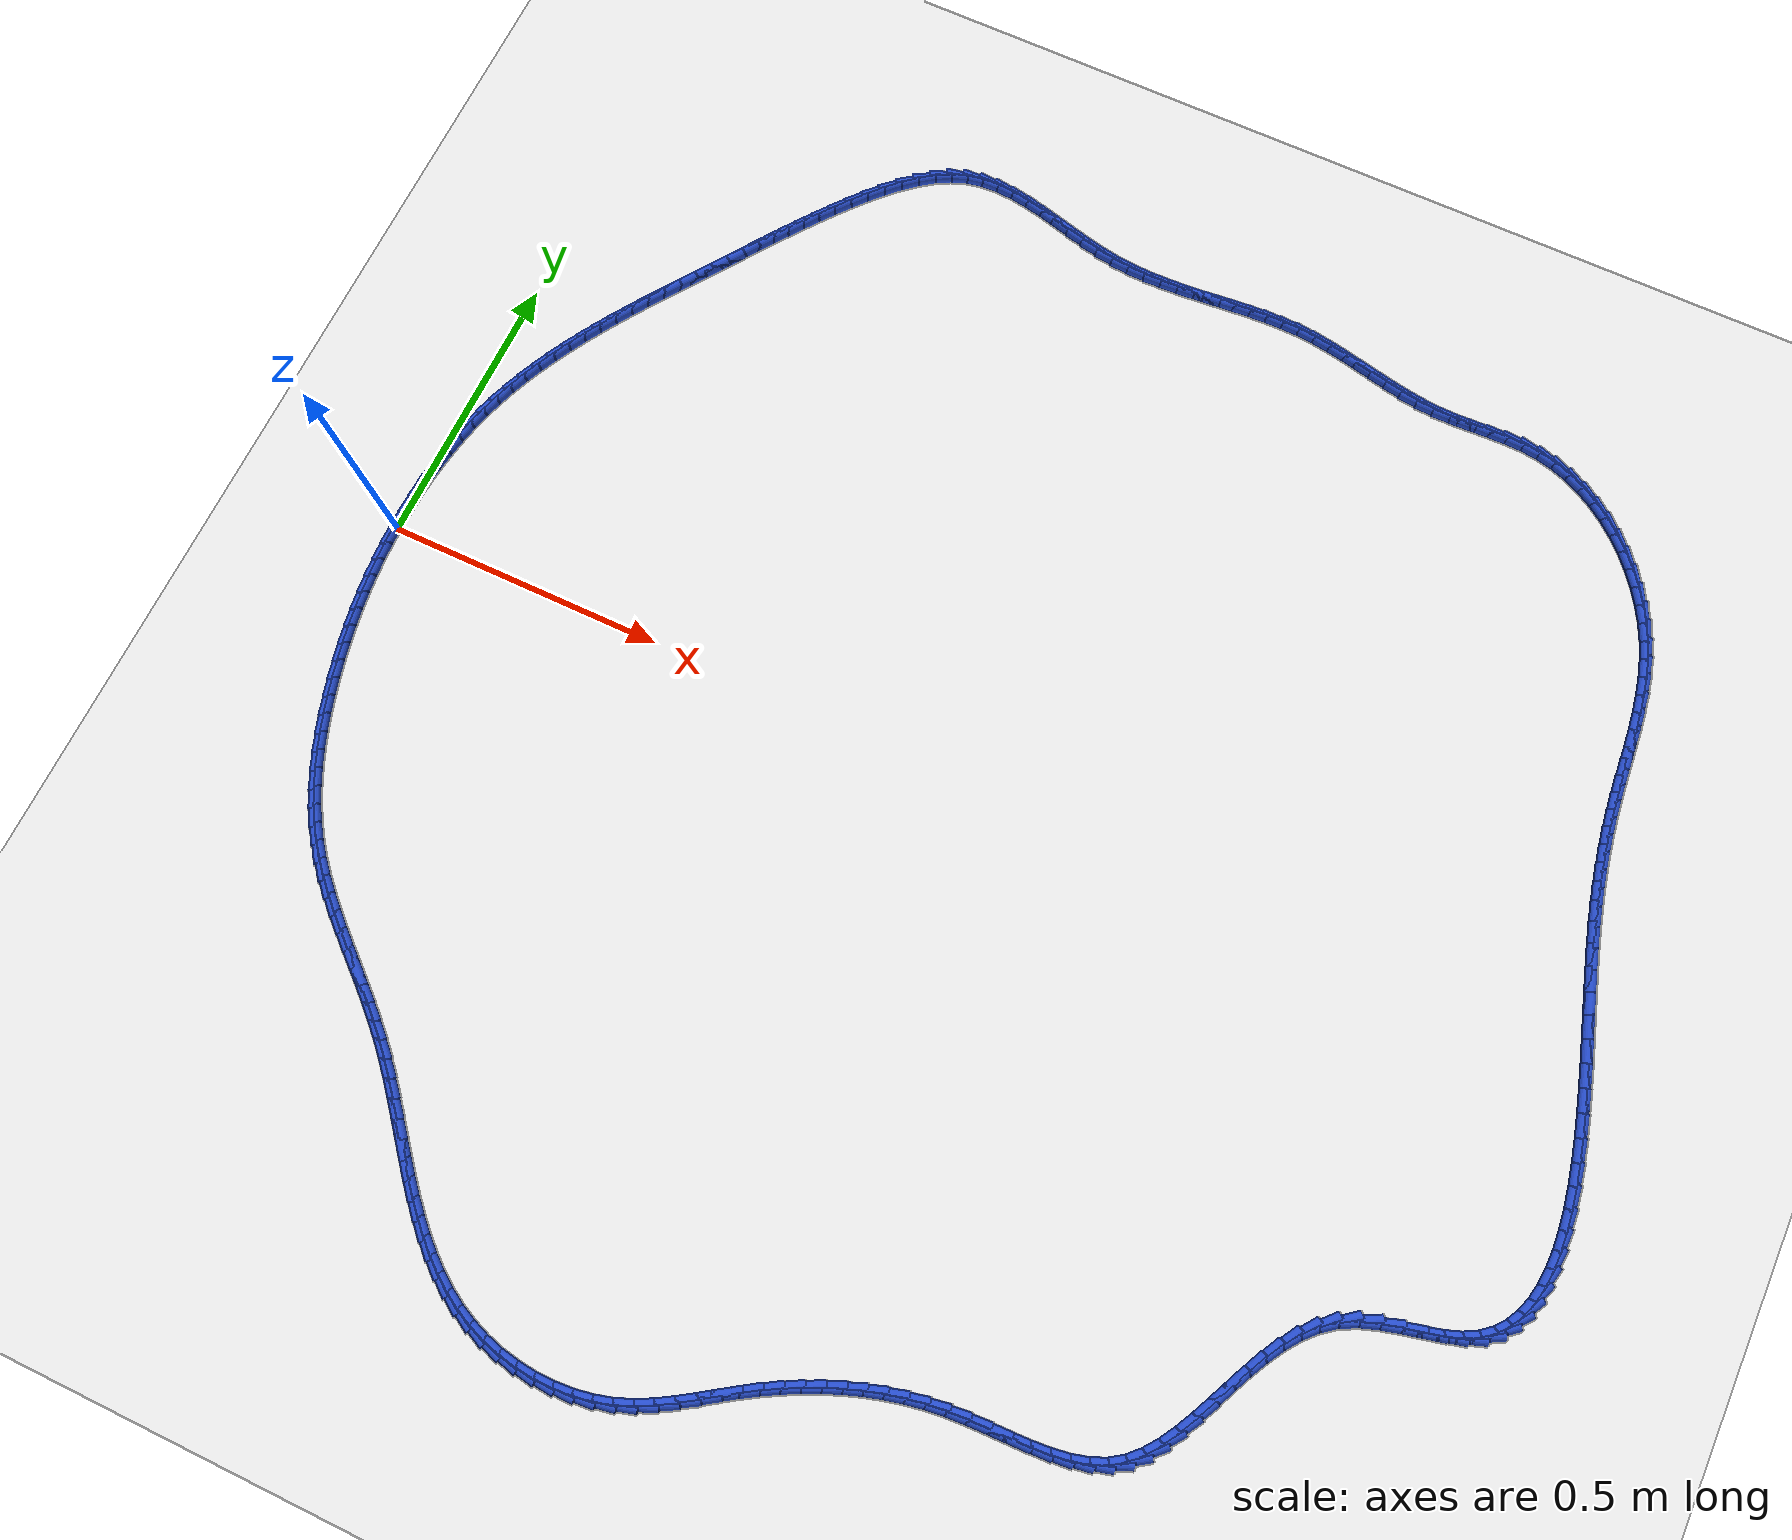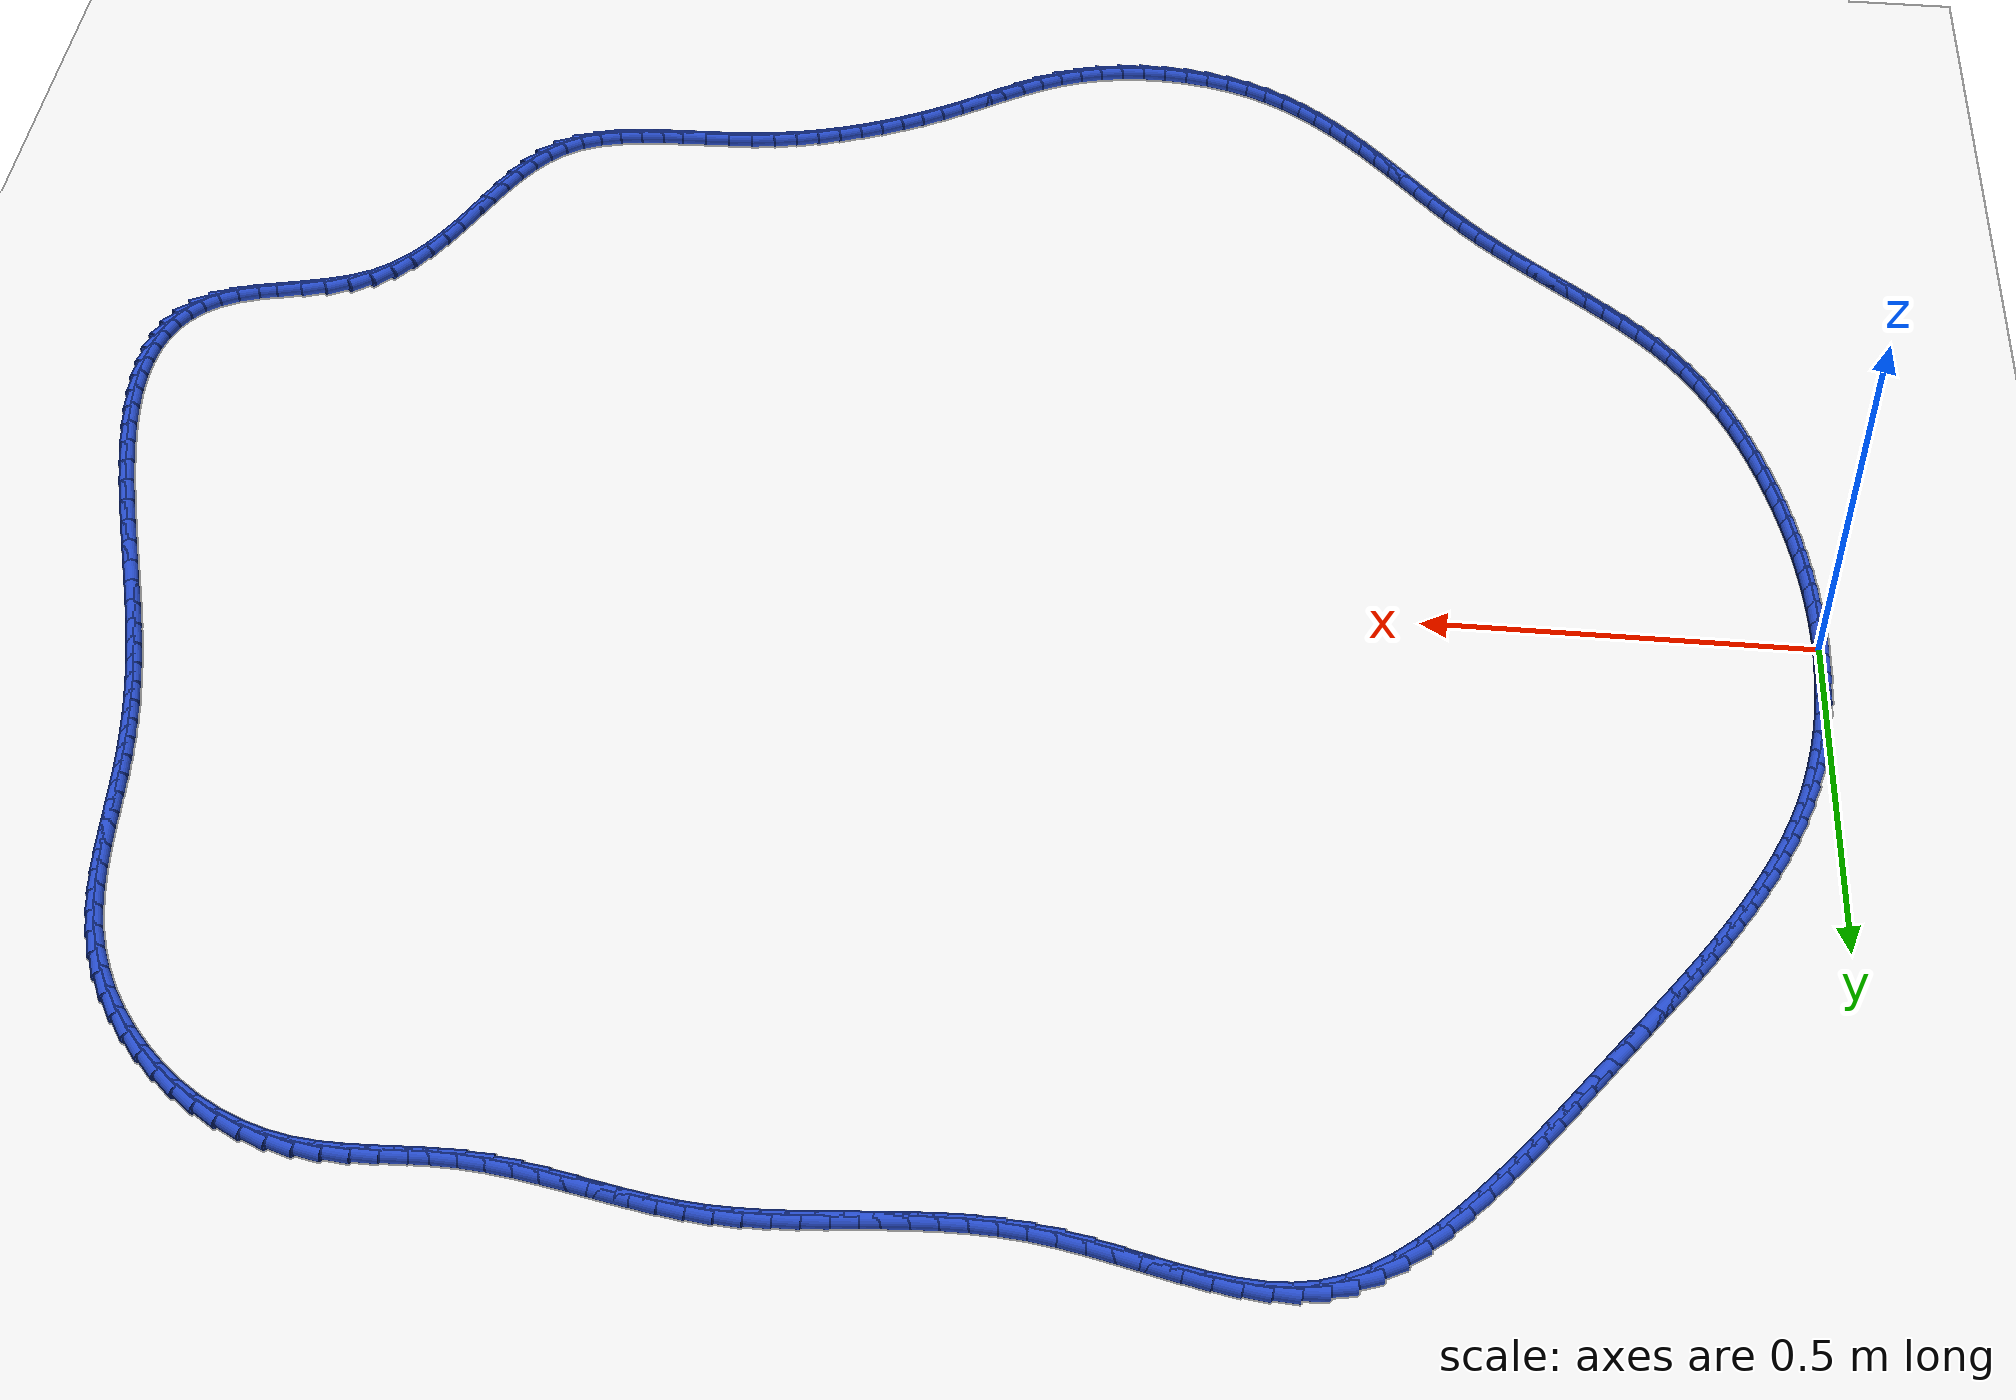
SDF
<sdf version="1.6">
 <world name="default">
  <light name="sun" type="directional">
   <pose>0 0 10 0 -0 0</pose>
   <diffuse>0.8 0.8 0.8 1</diffuse>
   <specular>0.2 0.2 0.2 1</specular>
   <attenuation>
    <range>1000</range>
    <constant>0.9</constant>
    <linear>0.01</linear>
    <quadratic>0.001</quadratic>
   </attenuation>
   <direction>-0.5 0.1 -0.9</direction>
  </light>
  <model name="ground_plane">
   <static>1</static>
   <link name="link">
    <collision name="collision">
     <geometry><plane><normal>0 0 1</normal><size>100 100</size></plane></geometry>
     <surface><friction><ode><mu>100</mu><mu2>50</mu2></ode></friction></surface>
    </collision>
    <visual name="visual">
     <cast_shadows>0</cast_shadows>
     <geometry><plane><normal>0 0 1</normal><size>100 100</size></plane></geometry>
     <material>
      <script><uri>file://media/materials/scripts/gazebo.material</uri><name>Gazebo/WhiteGlow</name></script>
     </material>
    </visual>
   </link>
  </model>
  <gravity>0 0 -9.8</gravity>
  <magnetic_field>6e-06 2.3e-05 -4.2e-05</magnetic_field>
  <atmosphere type="adiabatic"/>
  <physics name="default_physics" default="0" type="ode">
   <max_step_size>0.001</max_step_size>
   <real_time_factor>1</real_time_factor>
   <real_time_update_rate>1000</real_time_update_rate>
  </physics>
  <scene><ambient>0.4 0.4 0.4 1</ambient><background>0.7 0.7 0.7 1</background><shadows>1</shadows></scene>
  <spherical_coordinates>
   <surface_model>EARTH_WGS84</surface_model>
   <latitude_deg>0</latitude_deg>
   <longitude_deg>0</longitude_deg>
   <elevation>0</elevation>
   <heading_deg>0</heading_deg>
  </spherical_coordinates>
  <model name="line">
   <link name="link_0">
    <pose>6.938893903907228e-18 -5.551115123125783e-17 0.01 0 1.57 1.5669654835388633</pose>
    <collision name="collision">
     <geometry><cylinder><radius>0.01</radius><length>0.08</length></cylinder></geometry>
    </collision>
    <visual name="visual">
     <material>
      <script><name>Gazebo/Blue</name><uri>file://media/materials/scripts/gazebo.material</uri></script>
     </material>
     <geometry><cylinder><radius>0.01</radius><length>0.08</length></cylinder></geometry>
    </visual>
   </link>
   <link name="link_1">
    <pose>0.00012194123054519223 0.031831277315265846 0.01 0 1.57 1.535377310988925</pose>
    <collision name="collision">
     <geometry><cylinder><radius>0.01</radius><length>0.08</length></cylinder></geometry>
    </collision>
    <visual name="visual">
     <material>
      <script><name>Gazebo/Blue</name><uri>file://media/materials/scripts/gazebo.material</uri></script>
     </material>
     <geometry><cylinder><radius>0.01</radius><length>0.08</length></cylinder></geometry>
    </visual>
   </link>
   <link name="link_2">
    <pose>0.0012511948632218024 0.06370063756570017 0.01 0 1.57 1.5025588163627706</pose>
    <collision name="collision">
     <geometry><cylinder><radius>0.01</radius><length>0.08</length></cylinder></geometry>
    </collision>
    <visual name="visual">
     <material>
      <script><name>Gazebo/Blue</name><uri>file://media/materials/scripts/gazebo.material</uri></script>
     </material>
     <geometry><cylinder><radius>0.01</radius><length>0.08</length></cylinder></geometry>
    </visual>
   </link>
   <link name="link_3">
    <pose>0.003427320727243444 0.09554158830387062 0.01 0 1.57 1.4683853448257147</pose>
    <collision name="collision">
     <geometry><cylinder><radius>0.01</radius><length>0.08</length></cylinder></geometry>
    </collision>
    <visual name="visual">
     <material>
      <script><name>Gazebo/Blue</name><uri>file://media/materials/scripts/gazebo.material</uri></script>
     </material>
     <geometry><cylinder><radius>0.01</radius><length>0.08</length></cylinder></geometry>
    </visual>
   </link>
   <link name="link_4">
    <pose>0.006689878651823732 0.12728763708234492 0.01 0 1.57 1.4327346327322514</pose>
    <collision name="collision">
     <geometry><cylinder><radius>0.01</radius><length>0.08</length></cylinder></geometry>
    </collision>
    <visual name="visual">
     <material>
      <script><name>Gazebo/Blue</name><uri>file://media/materials/scripts/gazebo.material</uri></script>
     </material>
     <geometry><cylinder><radius>0.01</radius><length>0.08</length></cylinder></geometry>
    </visual>
   </link>
   <link name="link_5">
    <pose>0.01107842846617628 0.15887229145369067 0.01 0 1.57 1.3954884972912422</pose>
    <collision name="collision">
     <geometry><cylinder><radius>0.01</radius><length>0.08</length></cylinder></geometry>
    </collision>
    <visual name="visual">
     <material>
      <script><name>Gazebo/Blue</name><uri>file://media/materials/scripts/gazebo.material</uri></script>
     </material>
     <geometry><cylinder><radius>0.01</radius><length>0.08</length></cylinder></geometry>
    </visual>
   </link>
   <link name="link_6">
    <pose>0.016632529999514686 0.19022905897047548 0.01 0 1.57 1.356535224108454</pose>
    <collision name="collision">
     <geometry><cylinder><radius>0.01</radius><length>0.08</length></cylinder></geometry>
    </collision>
    <visual name="visual">
     <material>
      <script><name>Gazebo/Blue</name><uri>file://media/materials/scripts/gazebo.material</uri></script>
     </material>
     <geometry><cylinder><radius>0.01</radius><length>0.08</length></cylinder></geometry>
    </visual>
   </link>
   <link name="link_7">
    <pose>0.023391743081052574 0.22129144718526716 0.01 0 1.57 1.315772730758062</pose>
    <collision name="collision">
     <geometry><cylinder><radius>0.01</radius><length>0.08</length></cylinder></geometry>
    </collision>
    <visual name="visual">
     <material>
      <script><name>Gazebo/Blue</name><uri>file://media/materials/scripts/gazebo.material</uri></script>
     </material>
     <geometry><cylinder><radius>0.01</radius><length>0.08</length></cylinder></geometry>
    </visual>
   </link>
   <link name="link_8">
    <pose>0.03139562754000355 0.2519929636506333 0.01 0 1.57 1.2731125659442077</pose>
    <collision name="collision">
     <geometry><cylinder><radius>0.01</radius><length>0.08</length></cylinder></geometry>
    </collision>
    <visual name="visual">
     <material>
      <script><name>Gazebo/Blue</name><uri>file://media/materials/scripts/gazebo.material</uri></script>
     </material>
     <geometry><cylinder><radius>0.01</radius><length>0.08</length></cylinder></geometry>
    </visual>
   </link>
   <link name="link_9">
    <pose>0.04068374307144816 0.2822671160071291 0.01 0 1.57 1.2294073464821222</pose>
    <collision name="collision">
     <geometry><cylinder><radius>0.01</radius><length>0.08</length></cylinder></geometry>
    </collision>
    <visual name="visual">
     <material>
      <script><name>Gazebo/Blue</name><uri>file://media/materials/scripts/gazebo.material</uri></script>
     </material>
     <geometry><cylinder><radius>0.01</radius><length>0.08</length></cylinder></geometry>
    </visual>
   </link>
   <link name="link_10">
    <pose>0.051270545831827274 0.31206387912666805 0.01 0 1.57 1.1881747160021985</pose>
    <collision name="collision">
     <geometry><cylinder><radius>0.01</radius><length>0.08</length></cylinder></geometry>
    </collision>
    <visual name="visual">
     <material>
      <script><name>Gazebo/Blue</name><uri>file://media/materials/scripts/gazebo.material</uri></script>
     </material>
     <geometry><cylinder><radius>0.01</radius><length>0.08</length></cylinder></geometry>
    </visual>
   </link>
   <link name="link_11">
    <pose>0.06307529547825129 0.3413956741681762 0.01 0 1.57 1.150331695141347</pose>
    <collision name="collision">
     <geometry><cylinder><radius>0.01</radius><length>0.08</length></cylinder></geometry>
    </collision>
    <visual name="visual">
     <material>
      <script><name>Gazebo/Blue</name><uri>file://media/materials/scripts/gazebo.material</uri></script>
     </material>
     <geometry><cylinder><radius>0.01</radius><length>0.08</length></cylinder></geometry>
    </visual>
   </link>
   <link name="link_12">
    <pose>0.07599468984895631 0.3702897222236327 0.01 0 1.57 1.115922368008723</pose>
    <collision name="collision">
     <geometry><cylinder><radius>0.01</radius><length>0.08</length></cylinder></geometry>
    </collision>
    <visual name="visual">
     <material>
      <script><name>Gazebo/Blue</name><uri>file://media/materials/scripts/gazebo.material</uri></script>
     </material>
     <geometry><cylinder><radius>0.01</radius><length>0.08</length></cylinder></geometry>
    </visual>
   </link>
   <link name="link_13">
    <pose>0.08992542678217855 0.39877324438501704 0.01 0 1.57 1.084948609894714</pose>
    <collision name="collision">
     <geometry><cylinder><radius>0.01</radius><length>0.08</length></cylinder></geometry>
    </collision>
    <visual name="visual">
     <material>
      <script><name>Gazebo/Blue</name><uri>file://media/materials/scripts/gazebo.material</uri></script>
     </material>
     <geometry><cylinder><radius>0.01</radius><length>0.08</length></cylinder></geometry>
    </visual>
   </link>
   <link name="link_14">
    <pose>0.104764204116154 0.4268734617443082 0.01 0 1.57 1.0573823267352123</pose>
    <collision name="collision">
     <geometry><cylinder><radius>0.01</radius><length>0.08</length></cylinder></geometry>
    </collision>
    <visual name="visual">
     <material>
      <script><name>Gazebo/Blue</name><uri>file://media/materials/scripts/gazebo.material</uri></script>
     </material>
     <geometry><cylinder><radius>0.01</radius><length>0.08</length></cylinder></geometry>
    </visual>
   </link>
   <link name="link_15">
    <pose>0.1204077196891189 0.4546175953934856 0.01 0 1.57 1.0331765153796604</pose>
    <collision name="collision">
     <geometry><cylinder><radius>0.01</radius><length>0.08</length></cylinder></geometry>
    </collision>
    <visual name="visual">
     <material>
      <script><name>Gazebo/Blue</name><uri>file://media/materials/scripts/gazebo.material</uri></script>
     </material>
     <geometry><cylinder><radius>0.01</radius><length>0.08</length></cylinder></geometry>
    </visual>
   </link>
   <link name="link_16">
    <pose>0.1367526713393093 0.48203286642452847 0.01 0 1.57 1.0122748002317032</pose>
    <collision name="collision">
     <geometry><cylinder><radius>0.01</radius><length>0.08</length></cylinder></geometry>
    </collision>
    <visual name="visual">
     <material>
      <script><name>Gazebo/Blue</name><uri>file://media/materials/scripts/gazebo.material</uri></script>
     </material>
     <geometry><cylinder><radius>0.01</radius><length>0.08</length></cylinder></geometry>
    </visual>
   </link>
   <link name="link_17">
    <pose>0.15369575690496134 0.509146495929416 0.01 0 1.57 0.9946193721752303</pose>
    <collision name="collision">
     <geometry><cylinder><radius>0.01</radius><length>0.08</length></cylinder></geometry>
    </collision>
    <visual name="visual">
     <material>
      <script><name>Gazebo/Blue</name><uri>file://media/materials/scripts/gazebo.material</uri></script>
     </material>
     <geometry><cylinder><radius>0.01</radius><length>0.08</length></cylinder></geometry>
    </visual>
   </link>
   <link name="link_18">
    <pose>0.1711336742243111 0.535985705000127 0.01 0 1.57 0.9801574277149601</pose>
    <collision name="collision">
     <geometry><cylinder><radius>0.01</radius><length>0.08</length></cylinder></geometry>
    </collision>
    <visual name="visual">
     <material>
      <script><name>Gazebo/Blue</name><uri>file://media/materials/scripts/gazebo.material</uri></script>
     </material>
     <geometry><cylinder><radius>0.01</radius><length>0.08</length></cylinder></geometry>
    </visual>
   </link>
   <link name="link_19">
    <pose>0.18896312113559477 0.5625777147286413 0.01 0 1.57 0.9688462970841004</pose>
    <collision name="collision">
     <geometry><cylinder><radius>0.01</radius><length>0.08</length></cylinder></geometry>
    </collision>
    <visual name="visual">
     <material>
      <script><name>Gazebo/Blue</name><uri>file://media/materials/scripts/gazebo.material</uri></script>
     </material>
     <geometry><cylinder><radius>0.01</radius><length>0.08</length></cylinder></geometry>
    </visual>
   </link>
   <link name="link_20">
    <pose>0.2070807954770484 0.5889497462069377 0.01 0 1.57 0.9606574813904221</pose>
    <collision name="collision">
     <geometry><cylinder><radius>0.01</radius><length>0.08</length></cylinder></geometry>
    </collision>
    <visual name="visual">
     <material>
      <script><name>Gazebo/Blue</name><uri>file://media/materials/scripts/gazebo.material</uri></script>
     </material>
     <geometry><cylinder><radius>0.01</radius><length>0.08</length></cylinder></geometry>
    </visual>
   </link>
   <link name="link_21">
    <pose>0.22538339508690813 0.6151290205269958 0.01 0 1.57 0.955579810272203</pose>
    <collision name="collision">
     <geometry><cylinder><radius>0.01</radius><length>0.08</length></cylinder></geometry>
    </collision>
    <visual name="visual">
     <material>
      <script><name>Gazebo/Blue</name><uri>file://media/materials/scripts/gazebo.material</uri></script>
     </material>
     <geometry><cylinder><radius>0.01</radius><length>0.08</length></cylinder></geometry>
    </visual>
   </link>
   <link name="link_22">
    <pose>0.24376761780341016 0.6411427587807946 0.01 0 1.57 0.9536218977018835</pose>
    <collision name="collision">
     <geometry><cylinder><radius>0.01</radius><length>0.08</length></cylinder></geometry>
    </collision>
    <visual name="visual">
     <material>
      <script><name>Gazebo/Blue</name><uri>file://media/materials/scripts/gazebo.material</uri></script>
     </material>
     <geometry><cylinder><radius>0.01</radius><length>0.08</length></cylinder></geometry>
    </visual>
   </link>
   <link name="link_23">
    <pose>0.26213016146479046 0.6670181820603132 0.01 0 1.57 0.9548140238146458</pose>
    <collision name="collision">
     <geometry><cylinder><radius>0.01</radius><length>0.08</length></cylinder></geometry>
    </collision>
    <visual name="visual">
     <material>
      <script><name>Gazebo/Blue</name><uri>file://media/materials/scripts/gazebo.material</uri></script>
     </material>
     <geometry><cylinder><radius>0.01</radius><length>0.08</length></cylinder></geometry>
    </visual>
   </link>
   <link name="link_24">
    <pose>0.28036772390928544 0.6927825114575313 0.01 0 1.57 0.9582929610263923</pose>
    <collision name="collision">
     <geometry><cylinder><radius>0.01</radius><length>0.08</length></cylinder></geometry>
    </collision>
    <visual name="visual">
     <material>
      <script><name>Gazebo/Blue</name><uri>file://media/materials/scripts/gazebo.material</uri></script>
     </material>
     <geometry><cylinder><radius>0.01</radius><length>0.08</length></cylinder></geometry>
    </visual>
   </link>
   <link name="link_25">
    <pose>0.29841013017259904 0.7184601097069936 0.01 0 1.57 0.9593436651989775</pose>
    <collision name="collision">
     <geometry><cylinder><radius>0.01</radius><length>0.08</length></cylinder></geometry>
    </collision>
    <visual name="visual">
     <material>
      <script><name>Gazebo/Blue</name><uri>file://media/materials/scripts/gazebo.material</uri></script>
     </material>
     <geometry><cylinder><radius>0.01</radius><length>0.08</length></cylinder></geometry>
    </visual>
   </link>
   <link name="link_26">
    <pose>0.3163581970875961 0.744060585633713 0.01 0 1.57 0.9564043758296012</pose>
    <collision name="collision">
     <geometry><cylinder><radius>0.01</radius><length>0.08</length></cylinder></geometry>
    </collision>
    <visual name="visual">
     <material>
      <script><name>Gazebo/Blue</name><uri>file://media/materials/scripts/gazebo.material</uri></script>
     </material>
     <geometry><cylinder><radius>0.01</radius><length>0.08</length></cylinder></geometry>
    </visual>
   </link>
   <link name="link_27">
    <pose>0.33436775094205906 0.7695888016097443 0.01 0 1.57 0.9494918515290053</pose>
    <collision name="collision">
     <geometry><cylinder><radius>0.01</radius><length>0.08</length></cylinder></geometry>
    </collision>
    <visual name="visual">
     <material>
      <script><name>Gazebo/Blue</name><uri>file://media/materials/scripts/gazebo.material</uri></script>
     </material>
     <geometry><cylinder><radius>0.01</radius><length>0.08</length></cylinder></geometry>
    </visual>
   </link>
   <link name="link_28">
    <pose>0.35259464421295983 0.7950496177474264 0.01 0 1.57 0.938696021795991</pose>
    <collision name="collision">
     <geometry><cylinder><radius>0.01</radius><length>0.08</length></cylinder></geometry>
    </collision>
    <visual name="visual">
     <material>
      <script><name>Gazebo/Blue</name><uri>file://media/materials/scripts/gazebo.material</uri></script>
     </material>
     <geometry><cylinder><radius>0.01</radius><length>0.08</length></cylinder></geometry>
    </visual>
   </link>
   <link name="link_29">
    <pose>0.3711947293772703 0.8204478941590978 0.01 0 1.57 0.9241788284463602</pose>
    <collision name="collision">
     <geometry><cylinder><radius>0.01</radius><length>0.08</length></cylinder></geometry>
    </collision>
    <visual name="visual">
     <material>
      <script><name>Gazebo/Blue</name><uri>file://media/materials/scripts/gazebo.material</uri></script>
     </material>
     <geometry><cylinder><radius>0.01</radius><length>0.08</length></cylinder></geometry>
    </visual>
   </link>
   <link name="link_30">
    <pose>0.3903238589119627 0.8457884909570976 0.01 0 1.57 0.906171850045479</pose>
    <collision name="collision">
     <geometry><cylinder><radius>0.01</radius><length>0.08</length></cylinder></geometry>
    </collision>
    <visual name="visual">
     <material>
      <script><name>Gazebo/Blue</name><uri>file://media/materials/scripts/gazebo.material</uri></script>
     </material>
     <geometry><cylinder><radius>0.01</radius><length>0.08</length></cylinder></geometry>
    </visual>
   </link>
   <link name="link_31">
    <pose>0.4101378852940087 0.8710762682537642 0.01 0 1.57 0.884971522147805</pose>
    <collision name="collision">
     <geometry><cylinder><radius>0.01</radius><length>0.08</length></cylinder></geometry>
    </collision>
    <visual name="visual">
     <material>
      <script><name>Gazebo/Blue</name><uri>file://media/materials/scripts/gazebo.material</uri></script>
     </material>
     <geometry><cylinder><radius>0.01</radius><length>0.08</length></cylinder></geometry>
    </visual>
   </link>
   <link name="link_32">
    <pose>0.43079266100038055 0.8963160861614365 0.01 0 1.57 0.860325191939609</pose>
    <collision name="collision">
     <geometry><cylinder><radius>0.01</radius><length>0.08</length></cylinder></geometry>
    </collision>
    <visual name="visual">
     <material>
      <script><name>Gazebo/Blue</name><uri>file://media/materials/scripts/gazebo.material</uri></script>
     </material>
     <geometry><cylinder><radius>0.01</radius><length>0.08</length></cylinder></geometry>
    </visual>
   </link>
   <link name="link_33">
    <pose>0.4524358345052663 0.9214723815625939 0.01 0 1.57 0.8255889135785234</pose>
    <collision name="collision">
     <geometry><cylinder><radius>0.01</radius><length>0.08</length></cylinder></geometry>
    </collision>
    <visual name="visual">
     <material>
      <script><name>Gazebo/Blue</name><uri>file://media/materials/scripts/gazebo.material</uri></script>
     </material>
     <geometry><cylinder><radius>0.01</radius><length>0.08</length></cylinder></geometry>
    </visual>
   </link>
   <link name="link_34">
    <pose>0.4751241936718708 0.9460618977613874 0.01 0 1.57 0.7753351197922916</pose>
    <collision name="collision">
     <geometry><cylinder><radius>0.01</radius><length>0.08</length></cylinder></geometry>
    </collision>
    <visual name="visual">
     <material>
      <script><name>Gazebo/Blue</name><uri>file://media/materials/scripts/gazebo.material</uri></script>
     </material>
     <geometry><cylinder><radius>0.01</radius><length>0.08</length></cylinder></geometry>
    </visual>
   </link>
   <link name="link_35">
    <pose>0.49885797983272506 0.9693227587748456 0.01 0 1.57 0.7069330107999624</pose>
    <collision name="collision">
     <geometry><cylinder><radius>0.01</radius><length>0.08</length></cylinder></geometry>
    </collision>
    <visual name="visual">
     <material>
      <script><name>Gazebo/Blue</name><uri>file://media/materials/scripts/gazebo.material</uri></script>
     </material>
     <geometry><cylinder><radius>0.01</radius><length>0.08</length></cylinder></geometry>
    </visual>
   </link>
   <link name="link_36">
    <pose>0.5236365807927928 0.9904888830703481 0.01 0 1.57 0.6166618216930905</pose>
    <collision name="collision">
     <geometry><cylinder><radius>0.01</radius><length>0.08</length></cylinder></geometry>
    </collision>
    <visual name="visual">
     <material>
      <script><name>Gazebo/Blue</name><uri>file://media/materials/scripts/gazebo.material</uri></script>
     </material>
     <geometry><cylinder><radius>0.01</radius><length>0.08</length></cylinder></geometry>
    </visual>
   </link>
   <link name="link_37">
    <pose>0.5494593843570381 1.0087941891152745 0.01 0 1.57 0.5000352109031894</pose>
    <collision name="collision">
     <geometry><cylinder><radius>0.01</radius><length>0.08</length></cylinder></geometry>
    </collision>
    <visual name="visual">
     <material>
      <script><name>Gazebo/Blue</name><uri>file://media/materials/scripts/gazebo.material</uri></script>
     </material>
     <geometry><cylinder><radius>0.01</radius><length>0.08</length></cylinder></geometry>
    </visual>
   </link>
   <link name="link_38">
    <pose>0.5763257783304249 1.0234725953770047 0.01 0 1.57 0.35312439117154304</pose>
    <collision name="collision">
     <geometry><cylinder><radius>0.01</radius><length>0.08</length></cylinder></geometry>
    </collision>
    <visual name="visual">
     <material>
      <script><name>Gazebo/Blue</name><uri>file://media/materials/scripts/gazebo.material</uri></script>
     </material>
     <geometry><cylinder><radius>0.01</radius><length>0.08</length></cylinder></geometry>
    </visual>
   </link>
   <link name="link_39">
    <pose>0.6042350538172319 1.0337592078128153 0.01 0 1.57 0.18876865755380007</pose>
    <collision name="collision">
     <geometry><cylinder><radius>0.01</radius><length>0.08</length></cylinder></geometry>
    </collision>
    <visual name="visual">
     <material>
      <script><name>Gazebo/Blue</name><uri>file://media/materials/scripts/gazebo.material</uri></script>
     </material>
     <geometry><cylinder><radius>0.01</radius><length>0.08</length></cylinder></geometry>
    </visual>
   </link>
   <link name="link_40">
    <pose>0.633154343229614 1.0392840429426653 0.01 0 1.57 0.04550295876543548</pose>
    <collision name="collision">
     <geometry><cylinder><radius>0.01</radius><length>0.08</length></cylinder></geometry>
    </collision>
    <visual name="visual">
     <material>
      <script><name>Gazebo/Blue</name><uri>file://media/materials/scripts/gazebo.material</uri></script>
     </material>
     <geometry><cylinder><radius>0.01</radius><length>0.08</length></cylinder></geometry>
    </visual>
   </link>
   <link name="link_41">
    <pose>0.6629722235899185 1.0406417819274516 0.01 0 1.57 -0.06756325267002852</pose>
    <collision name="collision">
     <geometry><cylinder><radius>0.01</radius><length>0.08</length></cylinder></geometry>
    </collision>
    <visual name="visual">
     <material>
      <script><name>Gazebo/Blue</name><uri>file://media/materials/scripts/gazebo.material</uri></script>
     </material>
     <geometry><cylinder><radius>0.01</radius><length>0.08</length></cylinder></geometry>
    </visual>
   </link>
   <link name="link_42">
    <pose>0.6935655013087647 1.0385716497075008 0.01 0 1.57 -0.1511414407113176</pose>
    <collision name="collision">
     <geometry><cylinder><radius>0.01</radius><length>0.08</length></cylinder></geometry>
    </collision>
    <visual name="visual">
     <material>
      <script><name>Gazebo/Blue</name><uri>file://media/materials/scripts/gazebo.material</uri></script>
     </material>
     <geometry><cylinder><radius>0.01</radius><length>0.08</length></cylinder></geometry>
    </visual>
   </link>
   <link name="link_43">
    <pose>0.7248109827967707 1.0338128712231396 0.01 0 1.57 -0.20806371625510015</pose>
    <collision name="collision">
     <geometry><cylinder><radius>0.01</radius><length>0.08</length></cylinder></geometry>
    </collision>
    <visual name="visual">
     <material>
      <script><name>Gazebo/Blue</name><uri>file://media/materials/scripts/gazebo.material</uri></script>
     </material>
     <geometry><cylinder><radius>0.01</radius><length>0.08</length></cylinder></geometry>
    </visual>
   </link>
   <link name="link_44">
    <pose>0.7565854744645548 1.0271046714146934 0.01 0 1.57 -0.2412702136139695</pose>
    <collision name="collision">
     <geometry><cylinder><radius>0.01</radius><length>0.08</length></cylinder></geometry>
    </collision>
    <visual name="visual">
     <material>
      <script><name>Gazebo/Blue</name><uri>file://media/materials/scripts/gazebo.material</uri></script>
     </material>
     <geometry><cylinder><radius>0.01</radius><length>0.08</length></cylinder></geometry>
    </visual>
   </link>
   <link name="link_45">
    <pose>0.7887657827227358 1.0191862752224894 0.01 0 1.57 -0.2528961093170439</pose>
    <collision name="collision">
     <geometry><cylinder><radius>0.01</radius><length>0.08</length></cylinder></geometry>
    </collision>
    <visual name="visual">
     <material>
      <script><name>Gazebo/Blue</name><uri>file://media/materials/scripts/gazebo.material</uri></script>
     </material>
     <geometry><cylinder><radius>0.01</radius><length>0.08</length></cylinder></geometry>
    </visual>
   </link>
   <link name="link_46">
    <pose>0.8212287139819319 1.0107969075868535 0.01 0 1.57 -0.24398376004355413</pose>
    <collision name="collision">
     <geometry><cylinder><radius>0.01</radius><length>0.08</length></cylinder></geometry>
    </collision>
    <visual name="visual">
     <material>
      <script><name>Gazebo/Blue</name><uri>file://media/materials/scripts/gazebo.material</uri></script>
     </material>
     <geometry><cylinder><radius>0.01</radius><length>0.08</length></cylinder></geometry>
    </visual>
   </link>
   <link name="link_47">
    <pose>0.8538510746527614 1.0026757934481116 0.01 0 1.57 -0.2144682495640532</pose>
    <collision name="collision">
     <geometry><cylinder><radius>0.01</radius><length>0.08</length></cylinder></geometry>
    </collision>
    <visual name="visual">
     <material>
      <script><name>Gazebo/Blue</name><uri>file://media/materials/scripts/gazebo.material</uri></script>
     </material>
     <geometry><cylinder><radius>0.01</radius><length>0.08</length></cylinder></geometry>
    </visual>
   </link>
   <link name="link_48">
    <pose>0.8865096711458433 0.9955621577465913 0.01 0 1.57 -0.16332632293559765</pose>
    <collision name="collision">
     <geometry><cylinder><radius>0.01</radius><length>0.08</length></cylinder></geometry>
    </collision>
    <visual name="visual">
     <material>
      <script><name>Gazebo/Blue</name><uri>file://media/materials/scripts/gazebo.material</uri></script>
     </material>
     <geometry><cylinder><radius>0.01</radius><length>0.08</length></cylinder></geometry>
    </visual>
   </link>
   <link name="link_49">
    <pose>0.9190813948219791 0.9901945247162948 0.01 0 1.57 -0.0974655832915246</pose>
    <collision name="collision">
     <geometry><cylinder><radius>0.01</radius><length>0.08</length></cylinder></geometry>
    </collision>
    <visual name="visual">
     <material>
      <script><name>Gazebo/Blue</name><uri>file://media/materials/scripts/gazebo.material</uri></script>
     </material>
     <geometry><cylinder><radius>0.01</radius><length>0.08</length></cylinder></geometry>
    </visual>
   </link>
   <link name="link_50">
    <pose>0.9514776220580944 0.9870269710736745 0.01 0 1.57 -0.03825388709595281</pose>
    <collision name="collision">
     <geometry><cylinder><radius>0.01</radius><length>0.08</length></cylinder></geometry>
    </collision>
    <visual name="visual">
     <material>
      <script><name>Gazebo/Blue</name><uri>file://media/materials/scripts/gazebo.material</uri></script>
     </material>
     <geometry><cylinder><radius>0.01</radius><length>0.08</length></cylinder></geometry>
    </visual>
   </link>
   <link name="link_51">
    <pose>0.9836969845238246 0.9857938536627369 0.01 0 1.57 0.010094144254766724</pose>
    <collision name="collision">
     <geometry><cylinder><radius>0.01</radius><length>0.08</length></cylinder></geometry>
    </collision>
    <visual name="visual">
     <material>
      <script><name>Gazebo/Blue</name><uri>file://media/materials/scripts/gazebo.material</uri></script>
     </material>
     <geometry><cylinder><radius>0.01</radius><length>0.08</length></cylinder></geometry>
    </visual>
   </link>
   <link name="link_52">
    <pose>1.015751704305465 0.9861174296182401 0.01 0 1.57 0.0470629705185265</pose>
    <collision name="collision">
     <geometry><cylinder><radius>0.01</radius><length>0.08</length></cylinder></geometry>
    </collision>
    <visual name="visual">
     <material>
      <script><name>Gazebo/Blue</name><uri>file://media/materials/scripts/gazebo.material</uri></script>
     </material>
     <geometry><cylinder><radius>0.01</radius><length>0.08</length></cylinder></geometry>
    </visual>
   </link>
   <link name="link_53">
    <pose>1.0476540034893085 0.9876199560749416 0.01 0 1.57 0.0724041222366056</pose>
    <collision name="collision">
     <geometry><cylinder><radius>0.01</radius><length>0.08</length></cylinder></geometry>
    </collision>
    <visual name="visual">
     <material>
      <script><name>Gazebo/Blue</name><uri>file://media/materials/scripts/gazebo.material</uri></script>
     </material>
     <geometry><cylinder><radius>0.01</radius><length>0.08</length></cylinder></geometry>
    </visual>
   </link>
   <link name="link_54">
    <pose>1.0794161041616501 0.9899236901675994 0.01 0 1.57 0.08599803106822794</pose>
    <collision name="collision">
     <geometry><cylinder><radius>0.01</radius><length>0.08</length></cylinder></geometry>
    </collision>
    <visual name="visual">
     <material>
      <script><name>Gazebo/Blue</name><uri>file://media/materials/scripts/gazebo.material</uri></script>
     </material>
     <geometry><cylinder><radius>0.01</radius><length>0.08</length></cylinder></geometry>
    </visual>
   </link>
   <link name="link_55">
    <pose>1.1110502284087842 0.9926508890309718 0.01 0 1.57 0.08775198644588765</pose>
    <collision name="collision">
     <geometry><cylinder><radius>0.01</radius><length>0.08</length></cylinder></geometry>
    </collision>
    <visual name="visual">
     <material>
      <script><name>Gazebo/Blue</name><uri>file://media/materials/scripts/gazebo.material</uri></script>
     </material>
     <geometry><cylinder><radius>0.01</radius><length>0.08</length></cylinder></geometry>
    </visual>
   </link>
   <link name="link_56">
    <pose>1.142568598317004 0.9954238097998159 0.01 0 1.57 0.07754315158908005</pose>
    <collision name="collision">
     <geometry><cylinder><radius>0.01</radius><length>0.08</length></cylinder></geometry>
    </collision>
    <visual name="visual">
     <material>
      <script><name>Gazebo/Blue</name><uri>file://media/materials/scripts/gazebo.material</uri></script>
     </material>
     <geometry><cylinder><radius>0.01</radius><length>0.08</length></cylinder></geometry>
    </visual>
   </link>
   <link name="link_57">
    <pose>1.1739834359726047 0.9978647096088904 0.01 0 1.57 0.05521015154342319</pose>
    <collision name="collision">
     <geometry><cylinder><radius>0.01</radius><length>0.08</length></cylinder></geometry>
    </collision>
    <visual name="visual">
     <material>
      <script><name>Gazebo/Blue</name><uri>file://media/materials/scripts/gazebo.material</uri></script>
     </material>
     <geometry><cylinder><radius>0.01</radius><length>0.08</length></cylinder></geometry>
    </visual>
   </link>
   <link name="link_58">
    <pose>1.2053069634618794 0.9995958455929524 0.01 0 1.57 0.020596889794850914</pose>
    <collision name="collision">
     <geometry><cylinder><radius>0.01</radius><length>0.08</length></cylinder></geometry>
    </collision>
    <visual name="visual">
     <material>
      <script><name>Gazebo/Blue</name><uri>file://media/materials/scripts/gazebo.material</uri></script>
     </material>
     <geometry><cylinder><radius>0.01</radius><length>0.08</length></cylinder></geometry>
    </visual>
   </link>
   <link name="link_59">
    <pose>1.2365514028711233 1.0002394748867602 0.01 0 1.57 -0.02634682729325498</pose>
    <collision name="collision">
     <geometry><cylinder><radius>0.01</radius><length>0.08</length></cylinder></geometry>
    </collision>
    <visual name="visual">
     <material>
      <script><name>Gazebo/Blue</name><uri>file://media/materials/scripts/gazebo.material</uri></script>
     </material>
     <geometry><cylinder><radius>0.01</radius><length>0.08</length></cylinder></geometry>
    </visual>
   </link>
   <link name="link_60">
    <pose>1.2677289762866302 0.999417854625072 0.01 0 1.57 -0.0848402004805474</pose>
    <collision name="collision">
     <geometry><cylinder><radius>0.01</radius><length>0.08</length></cylinder></geometry>
    </collision>
    <visual name="visual">
     <material>
      <script><name>Gazebo/Blue</name><uri>file://media/materials/scripts/gazebo.material</uri></script>
     </material>
     <geometry><cylinder><radius>0.01</radius><length>0.08</length></cylinder></geometry>
    </visual>
   </link>
   <link name="link_61">
    <pose>1.2988522224955503 0.9967709985615213 0.01 0 1.57 -0.14102467265274782</pose>
    <collision name="collision">
     <geometry><cylinder><radius>0.01</radius><length>0.08</length></cylinder></geometry>
    </collision>
    <visual name="visual">
     <material>
      <script><name>Gazebo/Blue</name><uri>file://media/materials/scripts/gazebo.material</uri></script>
     </material>
     <geometry><cylinder><radius>0.01</radius><length>0.08</length></cylinder></geometry>
    </visual>
   </link>
   <link name="link_62">
    <pose>1.329941144060369 0.9923573955230051 0.01 0 1.57 -0.18129847067194396</pose>
    <collision name="collision">
     <geometry><cylinder><radius>0.01</radius><length>0.08</length></cylinder></geometry>
    </collision>
    <visual name="visual">
     <material>
      <script><name>Gazebo/Blue</name><uri>file://media/materials/scripts/gazebo.material</uri></script>
     </material>
     <geometry><cylinder><radius>0.01</radius><length>0.08</length></cylinder></geometry>
    </visual>
   </link>
   <link name="link_63">
    <pose>1.3610233085133334 0.9866596831261163 0.01 0 1.57 -0.2054088264379113</pose>
    <collision name="collision">
     <geometry><cylinder><radius>0.01</radius><length>0.08</length></cylinder></geometry>
    </collision>
    <visual name="visual">
     <material>
      <script><name>Gazebo/Blue</name><uri>file://media/materials/scripts/gazebo.material</uri></script>
     </material>
     <geometry><cylinder><radius>0.01</radius><length>0.08</length></cylinder></geometry>
    </visual>
   </link>
   <link name="link_64">
    <pose>1.3921266203275802 0.9801793904141248 0.01 0 1.57 -0.21372628012579523</pose>
    <collision name="collision">
     <geometry><cylinder><radius>0.01</radius><length>0.08</length></cylinder></geometry>
    </collision>
    <visual name="visual">
     <material>
      <script><name>Gazebo/Blue</name><uri>file://media/materials/scripts/gazebo.material</uri></script>
     </material>
     <geometry><cylinder><radius>0.01</radius><length>0.08</length></cylinder></geometry>
    </visual>
   </link>
   <link name="link_65">
    <pose>1.423278983976248 0.9734180464303004 0.01 0 1.57 -0.20646184336720474</pose>
    <collision name="collision">
     <geometry><cylinder><radius>0.01</radius><length>0.08</length></cylinder></geometry>
    </collision>
    <visual name="visual">
     <material>
      <script><name>Gazebo/Blue</name><uri>file://media/materials/scripts/gazebo.material</uri></script>
     </material>
     <geometry><cylinder><radius>0.01</radius><length>0.08</length></cylinder></geometry>
    </visual>
   </link>
   <link name="link_66">
    <pose>1.4545083039324764 0.9668771802179132 0.01 0 1.57 -0.1836116644949007</pose>
    <collision name="collision">
     <geometry><cylinder><radius>0.01</radius><length>0.08</length></cylinder></geometry>
    </collision>
    <visual name="visual">
     <material>
      <script><name>Gazebo/Blue</name><uri>file://media/materials/scripts/gazebo.material</uri></script>
     </material>
     <geometry><cylinder><radius>0.01</radius><length>0.08</length></cylinder></geometry>
    </visual>
   </link>
   <link name="link_67">
    <pose>1.485842484669402 0.9610583208202332 0.01 0 1.57 -0.14501145572093538</pose>
    <collision name="collision">
     <geometry><cylinder><radius>0.01</radius><length>0.08</length></cylinder></geometry>
    </collision>
    <visual name="visual">
     <material>
      <script><name>Gazebo/Blue</name><uri>file://media/materials/scripts/gazebo.material</uri></script>
     </material>
     <geometry><cylinder><radius>0.01</radius><length>0.08</length></cylinder></geometry>
    </visual>
   </link>
   <link name="link_68">
    <pose>1.5173094306601644 0.9564629972805305 0.01 0 1.57 -0.0905037448146181</pose>
    <collision name="collision">
     <geometry><cylinder><radius>0.01</radius><length>0.08</length></cylinder></geometry>
    </collision>
    <visual name="visual">
     <material>
      <script><name>Gazebo/Blue</name><uri>file://media/materials/scripts/gazebo.material</uri></script>
     </material>
     <geometry><cylinder><radius>0.01</radius><length>0.08</length></cylinder></geometry>
    </visual>
   </link>
   <link name="link_69">
    <pose>1.5489370463779009 0.9535927386420745 0.01 0 1.57 -0.023188830017155403</pose>
    <collision name="collision">
     <geometry><cylinder><radius>0.01</radius><length>0.08</length></cylinder></geometry>
    </collision>
    <visual name="visual">
     <material>
      <script><name>Gazebo/Blue</name><uri>file://media/materials/scripts/gazebo.material</uri></script>
     </material>
     <geometry><cylinder><radius>0.01</radius><length>0.08</length></cylinder></geometry>
    </visual>
   </link>
   <link name="link_70">
    <pose>1.5807444389985381 0.9528550301892503 0.01 0 1.57 0.027182631395976594</pose>
    <collision name="collision">
     <geometry><cylinder><radius>0.01</radius><length>0.08</length></cylinder></geometry>
    </collision>
    <visual name="visual">
     <material>
      <script><name>Gazebo/Blue</name><uri>file://media/materials/scripts/gazebo.material</uri></script>
     </material>
     <geometry><cylinder><radius>0.01</radius><length>0.08</length></cylinder></geometry>
    </visual>
   </link>
   <link name="link_71">
    <pose>1.612663300531228 0.9537228825981346 0.01 0 1.57 0.04419482162252456</pose>
    <collision name="collision">
     <geometry><cylinder><radius>0.01</radius><length>0.08</length></cylinder></geometry>
    </collision>
    <visual name="visual">
     <material>
      <script><name>Gazebo/Blue</name><uri>file://media/materials/scripts/gazebo.material</uri></script>
     </material>
     <geometry><cylinder><radius>0.01</radius><length>0.08</length></cylinder></geometry>
    </visual>
   </link>
   <link name="link_72">
    <pose>1.6445752614434126 0.9551341449554698 0.01 0 1.57 0.027873031226642954</pose>
    <collision name="collision">
     <geometry><cylinder><radius>0.01</radius><length>0.08</length></cylinder></geometry>
    </collision>
    <visual name="visual">
     <material>
      <script><name>Gazebo/Blue</name><uri>file://media/materials/scripts/gazebo.material</uri></script>
     </material>
     <geometry><cylinder><radius>0.01</radius><length>0.08</length></cylinder></geometry>
    </visual>
   </link>
   <link name="link_73">
    <pose>1.6763613612872674 0.9560203494200283 0.01 0 1.57 -0.02242149887177784</pose>
    <collision name="collision">
     <geometry><cylinder><radius>0.01</radius><length>0.08</length></cylinder></geometry>
    </collision>
    <visual name="visual">
     <material>
      <script><name>Gazebo/Blue</name><uri>file://media/materials/scripts/gazebo.material</uri></script>
     </material>
     <geometry><cylinder><radius>0.01</radius><length>0.08</length></cylinder></geometry>
    </visual>
   </link>
   <link name="link_74">
    <pose>1.7079026396149688 0.9553130281505823 0.01 0 1.57 -0.10765102381634747</pose>
    <collision name="collision">
     <geometry><cylinder><radius>0.01</radius><length>0.08</length></cylinder></geometry>
    </collision>
    <visual name="visual">
     <material>
      <script><name>Gazebo/Blue</name><uri>file://media/materials/scripts/gazebo.material</uri></script>
     </material>
     <geometry><cylinder><radius>0.01</radius><length>0.08</length></cylinder></geometry>
    </visual>
   </link>
   <link name="link_75">
    <pose>1.7390801359786912 0.9519437133059039 0.01 0 1.57 -0.2205212773113578</pose>
    <collision name="collision">
     <geometry><cylinder><radius>0.01</radius><length>0.08</length></cylinder></geometry>
    </collision>
    <visual name="visual">
     <material>
      <script><name>Gazebo/Blue</name><uri>file://media/materials/scripts/gazebo.material</uri></script>
     </material>
     <geometry><cylinder><radius>0.01</radius><length>0.08</length></cylinder></geometry>
    </visual>
   </link>
   <link name="link_76">
    <pose>1.7697646347118712 0.9450652665101434 0.01 0 1.57 -0.3317823296719829</pose>
    <collision name="collision">
     <geometry><cylinder><radius>0.01</radius><length>0.08</length></cylinder></geometry>
    </collision>
    <visual name="visual">
     <material>
      <script><name>Gazebo/Blue</name><uri>file://media/materials/scripts/gazebo.material</uri></script>
     </material>
     <geometry><cylinder><radius>0.01</radius><length>0.08</length></cylinder></geometry>
    </visual>
   </link>
   <link name="link_77">
    <pose>1.7997855909751648 0.9347225209726223 0.01 0 1.57 -0.4344257023588785</pose>
    <collision name="collision">
     <geometry><cylinder><radius>0.01</radius><length>0.08</length></cylinder></geometry>
    </collision>
    <visual name="visual">
     <material>
      <script><name>Gazebo/Blue</name><uri>file://media/materials/scripts/gazebo.material</uri></script>
     </material>
     <geometry><cylinder><radius>0.01</radius><length>0.08</length></cylinder></geometry>
    </visual>
   </link>
   <link name="link_78">
    <pose>1.8289620499832029 0.9211849787125048 0.01 0 1.57 -0.5291714408558121</pose>
    <collision name="collision">
     <geometry><cylinder><radius>0.01</radius><length>0.08</length></cylinder></geometry>
    </collision>
    <visual name="visual">
     <material>
      <script><name>Gazebo/Blue</name><uri>file://media/materials/scripts/gazebo.material</uri></script>
     </material>
     <geometry><cylinder><radius>0.01</radius><length>0.08</length></cylinder></geometry>
    </visual>
   </link>
   <link name="link_79">
    <pose>1.8571130569504533 0.9047221417524219 0.01 0 1.57 -0.6171088332450005</pose>
    <collision name="collision">
     <geometry><cylinder><radius>0.01</radius><length>0.08</length></cylinder></geometry>
    </collision>
    <visual name="visual">
     <material>
      <script><name>Gazebo/Blue</name><uri>file://media/materials/scripts/gazebo.material</uri></script>
     </material>
     <geometry><cylinder><radius>0.01</radius><length>0.08</length></cylinder></geometry>
    </visual>
   </link>
   <link name="link_80">
    <pose>1.884057657091386 0.8856035121150049 0.01 0 1.57 -0.6995043630200591</pose>
    <collision name="collision">
     <geometry><cylinder><radius>0.01</radius><length>0.08</length></cylinder></geometry>
    </collision>
    <visual name="visual">
     <material>
      <script><name>Gazebo/Blue</name><uri>file://media/materials/scripts/gazebo.material</uri></script>
     </material>
     <geometry><cylinder><radius>0.01</radius><length>0.08</length></cylinder></geometry>
    </visual>
   </link>
   <link name="link_81">
    <pose>1.909614895620469 0.8640985918228846 0.01 0 1.57 -0.7776854757467255</pose>
    <collision name="collision">
     <geometry><cylinder><radius>0.01</radius><length>0.08</length></cylinder></geometry>
    </collision>
    <visual name="visual">
     <material>
      <script><name>Gazebo/Blue</name><uri>file://media/materials/scripts/gazebo.material</uri></script>
     </material>
     <geometry><cylinder><radius>0.01</radius><length>0.08</length></cylinder></geometry>
    </visual>
   </link>
   <link name="link_82">
    <pose>1.9336038177521715 0.8404768828986923 0.01 0 1.57 -0.8529839425820859</pose>
    <collision name="collision">
     <geometry><cylinder><radius>0.01</radius><length>0.08</length></cylinder></geometry>
    </collision>
    <visual name="visual">
     <material>
      <script><name>Gazebo/Blue</name><uri>file://media/materials/scripts/gazebo.material</uri></script>
     </material>
     <geometry><cylinder><radius>0.01</radius><length>0.08</length></cylinder></geometry>
    </visual>
   </link>
   <link name="link_83">
    <pose>1.9558434687009618 0.8150078873650584 0.01 0 1.57 -0.9267195190886793</pose>
    <collision name="collision">
     <geometry><cylinder><radius>0.01</radius><length>0.08</length></cylinder></geometry>
    </collision>
    <visual name="visual">
     <material>
      <script><name>Gazebo/Blue</name><uri>file://media/materials/scripts/gazebo.material</uri></script>
     </material>
     <geometry><cylinder><radius>0.01</radius><length>0.08</length></cylinder></geometry>
    </visual>
   </link>
   <link name="link_84">
    <pose>1.9761528936813095 0.7879611072446151 0.01 0 1.57 -1.000208095487081</pose>
    <collision name="collision">
     <geometry><cylinder><radius>0.01</radius><length>0.08</length></cylinder></geometry>
    </collision>
    <visual name="visual">
     <material>
      <script><name>Gazebo/Blue</name><uri>file://media/materials/scripts/gazebo.material</uri></script>
     </material>
     <geometry><cylinder><radius>0.01</radius><length>0.08</length></cylinder></geometry>
    </visual>
   </link>
   <link name="link_85">
    <pose>1.9943511379076835 0.7596060445599923 0.01 0 1.57 -1.0747828481990753</pose>
    <collision name="collision">
     <geometry><cylinder><radius>0.01</radius><length>0.08</length></cylinder></geometry>
    </collision>
    <visual name="visual">
     <material>
      <script><name>Gazebo/Blue</name><uri>file://media/materials/scripts/gazebo.material</uri></script>
     </material>
     <geometry><cylinder><radius>0.01</radius><length>0.08</length></cylinder></geometry>
    </visual>
   </link>
   <link name="link_86">
    <pose>2.010257246594552 0.7302122013338221 0.01 0 1.57 -1.1518187392249741</pose>
    <collision name="collision">
     <geometry><cylinder><radius>0.01</radius><length>0.08</length></cylinder></geometry>
    </collision>
    <visual name="visual">
     <material>
      <script><name>Gazebo/Blue</name><uri>file://media/materials/scripts/gazebo.material</uri></script>
     </material>
     <geometry><cylinder><radius>0.01</radius><length>0.08</length></cylinder></geometry>
    </visual>
   </link>
   <link name="link_87">
    <pose>2.0236903008292 0.7000490692684568 0.01 0 1.57 -1.2298455330077913</pose>
    <collision name="collision">
     <geometry><cylinder><radius>0.01</radius><length>0.08</length></cylinder></geometry>
    </collision>
    <visual name="visual">
     <material>
      <script><name>Gazebo/Blue</name><uri>file://media/materials/scripts/gazebo.material</uri></script>
     </material>
     <geometry><cylinder><radius>0.01</radius><length>0.08</length></cylinder></geometry>
    </visual>
   </link>
   <link name="link_88">
    <pose>2.0345811295196503 0.6693539912492867 0.01 0 1.57 -1.2998049500466524</pose>
    <collision name="collision">
     <geometry><cylinder><radius>0.01</radius><length>0.08</length></cylinder></geometry>
    </collision>
    <visual name="visual">
     <material>
      <script><name>Gazebo/Blue</name><uri>file://media/materials/scripts/gazebo.material</uri></script>
     </material>
     <geometry><cylinder><radius>0.01</radius><length>0.08</length></cylinder></geometry>
    </visual>
   </link>
   <link name="link_89">
    <pose>2.0432195541368796 0.6382610313136557 0.01 0 1.57 -1.3589705079030918</pose>
    <collision name="collision">
     <geometry><cylinder><radius>0.01</radius><length>0.08</length></cylinder></geometry>
    </collision>
    <visual name="visual">
     <material>
      <script><name>Gazebo/Blue</name><uri>file://media/materials/scripts/gazebo.material</uri></script>
     </material>
     <geometry><cylinder><radius>0.01</radius><length>0.08</length></cylinder></geometry>
    </visual>
   </link>
   <link name="link_90">
    <pose>2.0499673416638124 0.6068835554389409 0.01 0 1.57 -1.4068564324336597</pose>
    <collision name="collision">
     <geometry><cylinder><radius>0.01</radius><length>0.08</length></cylinder></geometry>
    </collision>
    <visual name="visual">
     <material>
      <script><name>Gazebo/Blue</name><uri>file://media/materials/scripts/gazebo.material</uri></script>
     </material>
     <geometry><cylinder><radius>0.01</radius><length>0.08</length></cylinder></geometry>
    </visual>
   </link>
   <link name="link_91">
    <pose>2.0551862590833725 0.5753349296025176 0.01 0 1.57 -1.4432957808813394</pose>
    <collision name="collision">
     <geometry><cylinder><radius>0.01</radius><length>0.08</length></cylinder></geometry>
    </collision>
    <visual name="visual">
     <material>
      <script><name>Gazebo/Blue</name><uri>file://media/materials/scripts/gazebo.material</uri></script>
     </material>
     <geometry><cylinder><radius>0.01</radius><length>0.08</length></cylinder></geometry>
    </visual>
   </link>
   <link name="link_92">
    <pose>2.059238073378485 0.543728519781763 0.01 0 1.57 -1.4682604191956454</pose>
    <collision name="collision">
     <geometry><cylinder><radius>0.01</radius><length>0.08</length></cylinder></geometry>
    </collision>
    <visual name="visual">
     <material>
      <script><name>Gazebo/Blue</name><uri>file://media/materials/scripts/gazebo.material</uri></script>
     </material>
     <geometry><cylinder><radius>0.01</radius><length>0.08</length></cylinder></geometry>
    </visual>
   </link>
   <link name="link_93">
    <pose>2.062484551532075 0.5121776919540528 0.01 0 1.57 -1.4817165395546767</pose>
    <collision name="collision">
     <geometry><cylinder><radius>0.01</radius><length>0.08</length></cylinder></geometry>
    </collision>
    <visual name="visual">
     <material>
      <script><name>Gazebo/Blue</name><uri>file://media/materials/scripts/gazebo.material</uri></script>
     </material>
     <geometry><cylinder><radius>0.01</radius><length>0.08</length></cylinder></geometry>
    </visual>
   </link>
   <link name="link_94">
    <pose>2.0652874605270664 0.48079581209676375 0.01 0 1.57 -1.4835219707570435</pose>
    <collision name="collision">
     <geometry><cylinder><radius>0.01</radius><length>0.08</length></cylinder></geometry>
    </collision>
    <visual name="visual">
     <material>
      <script><name>Gazebo/Blue</name><uri>file://media/materials/scripts/gazebo.material</uri></script>
     </material>
     <geometry><cylinder><radius>0.01</radius><length>0.08</length></cylinder></geometry>
    </visual>
   </link>
   <link name="link_95">
    <pose>2.068008567346383 0.4496962461872714 0.01 0 1.57 -1.4733688259489817</pose>
    <collision name="collision">
     <geometry><cylinder><radius>0.01</radius><length>0.08</length></cylinder></geometry>
    </collision>
    <visual name="visual">
     <material>
      <script><name>Gazebo/Blue</name><uri>file://media/materials/scripts/gazebo.material</uri></script>
     </material>
     <geometry><cylinder><radius>0.01</radius><length>0.08</length></cylinder></geometry>
    </visual>
   </link>
   <link name="link_96">
    <pose>2.0710094878865077 0.4189921896361074 0.01 0 1.57 -1.4535699312417452</pose>
    <collision name="collision">
     <geometry><cylinder><radius>0.01</radius><length>0.08</length></cylinder></geometry>
    </collision>
    <visual name="visual">
     <material>
      <script><name>Gazebo/Blue</name><uri>file://media/materials/scripts/gazebo.material</uri></script>
     </material>
     <geometry><cylinder><radius>0.01</radius><length>0.08</length></cylinder></geometry>
    </visual>
   </link>
   <link name="link_97">
    <pose>2.0745756175117434 0.38871078979115625 0.01 0 1.57 -1.4314084883542386</pose>
    <collision name="collision">
     <geometry><cylinder><radius>0.01</radius><length>0.08</length></cylinder></geometry>
    </collision>
    <visual name="visual">
     <material>
      <script><name>Gazebo/Blue</name><uri>file://media/materials/scripts/gazebo.material</uri></script>
     </material>
     <geometry><cylinder><radius>0.01</radius><length>0.08</length></cylinder></geometry>
    </visual>
   </link>
   <link name="link_98">
    <pose>2.078792563534171 0.358653646180805 0.01 0 1.57 -1.408569980438844</pose>
    <collision name="collision">
     <geometry><cylinder><radius>0.01</radius><length>0.08</length></cylinder></geometry>
    </collision>
    <visual name="visual">
     <material>
      <script><name>Gazebo/Blue</name><uri>file://media/materials/scripts/gazebo.material</uri></script>
     </material>
     <geometry><cylinder><radius>0.01</radius><length>0.08</length></cylinder></geometry>
    </visual>
   </link>
   <link name="link_99">
    <pose>2.083713597267178 0.32858585307741933 0.01 0 1.57 -1.3856191985760256</pose>
    <collision name="collision">
     <geometry><cylinder><radius>0.01</radius><length>0.08</length></cylinder></geometry>
    </collision>
    <visual name="visual">
     <material>
      <script><name>Gazebo/Blue</name><uri>file://media/materials/scripts/gazebo.material</uri></script>
     </material>
     <geometry><cylinder><radius>0.01</radius><length>0.08</length></cylinder></geometry>
    </visual>
   </link>
   <link name="link_100">
    <pose>2.08939199002415 0.2982725047533635 0.01 0 1.57 -1.3631099295155278</pose>
    <collision name="collision">
     <geometry><cylinder><radius>0.01</radius><length>0.08</length></cylinder></geometry>
    </collision>
    <visual name="visual">
     <material>
      <script><name>Gazebo/Blue</name><uri>file://media/materials/scripts/gazebo.material</uri></script>
     </material>
     <geometry><cylinder><radius>0.01</radius><length>0.08</length></cylinder></geometry>
    </visual>
   </link>
   <link name="link_101">
    <pose>2.0958810131184777 0.26747869548100356 0.01 0 1.57 -1.3415408060444778</pose>
    <collision name="collision">
     <geometry><cylinder><radius>0.01</radius><length>0.08</length></cylinder></geometry>
    </collision>
    <visual name="visual">
     <material>
      <script><name>Gazebo/Blue</name><uri>file://media/materials/scripts/gazebo.material</uri></script>
     </material>
     <geometry><cylinder><radius>0.01</radius><length>0.08</length></cylinder></geometry>
    </visual>
   </link>
   <link name="link_102">
    <pose>2.1032339378635454 0.23596951953270384 0.01 0 1.57 -1.321321625853663</pose>
    <collision name="collision">
     <geometry><cylinder><radius>0.01</radius><length>0.08</length></cylinder></geometry>
    </collision>
    <visual name="visual">
     <material>
      <script><name>Gazebo/Blue</name><uri>file://media/materials/scripts/gazebo.material</uri></script>
     </material>
     <geometry><cylinder><radius>0.01</radius><length>0.08</length></cylinder></geometry>
    </visual>
   </link>
   <link name="link_103">
    <pose>2.111504035572742 0.20351007118083014 0.01 0 1.57 -1.302755090681027</pose>
    <collision name="collision">
     <geometry><cylinder><radius>0.01</radius><length>0.08</length></cylinder></geometry>
    </collision>
    <visual name="visual">
     <material>
      <script><name>Gazebo/Blue</name><uri>file://media/materials/scripts/gazebo.material</uri></script>
     </material>
     <geometry><cylinder><radius>0.01</radius><length>0.08</length></cylinder></geometry>
    </visual>
   </link>
   <link name="link_104">
    <pose>2.120744527624089 0.16986552031682525 0.01 0 1.57 -1.2870370394047246</pose>
    <collision name="collision">
     <geometry><cylinder><radius>0.01</radius><length>0.08</length></cylinder></geometry>
    </collision>
    <visual name="visual">
     <material>
      <script><name>Gazebo/Blue</name><uri>file://media/materials/scripts/gazebo.material</uri></script>
     </material>
     <geometry><cylinder><radius>0.01</radius><length>0.08</length></cylinder></geometry>
    </visual>
   </link>
   <link name="link_105">
    <pose>2.1309400585017158 0.13490488550534788 0.01 0 1.57 -1.2767669157736463</pose>
    <collision name="collision">
     <geometry><cylinder><radius>0.01</radius><length>0.08</length></cylinder></geometry>
    </collision>
    <visual name="visual">
     <material>
      <script><name>Gazebo/Blue</name><uri>file://media/materials/scripts/gazebo.material</uri></script>
     </material>
     <geometry><cylinder><radius>0.01</radius><length>0.08</length></cylinder></geometry>
    </visual>
   </link>
   <link name="link_106">
    <pose>2.1418707614286516 0.09880688471442109 0.01 0 1.57 -1.2717125280725057</pose>
    <collision name="collision">
     <geometry><cylinder><radius>0.01</radius><length>0.08</length></cylinder></geometry>
    </collision>
    <visual name="visual">
     <material>
      <script><name>Gazebo/Blue</name><uri>file://media/materials/scripts/gazebo.material</uri></script>
     </material>
     <geometry><cylinder><radius>0.01</radius><length>0.08</length></cylinder></geometry>
    </visual>
   </link>
   <link name="link_107">
    <pose>2.1532788146665616 0.06180771259489985 0.01 0 1.57 -1.2713611393586757</pose>
    <collision name="collision">
     <geometry><cylinder><radius>0.01</radius><length>0.08</length></cylinder></geometry>
    </collision>
    <visual name="visual">
     <material>
      <script><name>Gazebo/Blue</name><uri>file://media/materials/scripts/gazebo.material</uri></script>
     </material>
     <geometry><cylinder><radius>0.01</radius><length>0.08</length></cylinder></geometry>
    </visual>
   </link>
   <link name="link_108">
    <pose>2.164906396477109 0.02414356379763686 0.01 0 1.57 -1.2754566917188483</pose>
    <collision name="collision">
     <geometry><cylinder><radius>0.01</radius><length>0.08</length></cylinder></geometry>
    </collision>
    <visual name="visual">
     <material>
      <script><name>Gazebo/Blue</name><uri>file://media/materials/scripts/gazebo.material</uri></script>
     </material>
     <geometry><cylinder><radius>0.01</radius><length>0.08</length></cylinder></geometry>
    </visual>
   </link>
   <link name="link_109">
    <pose>2.1764956851219592 -0.013949367026513091 0.01 0 1.57 -1.2839583065396747</pose>
    <collision name="collision">
     <geometry><cylinder><radius>0.01</radius><length>0.08</length></cylinder></geometry>
    </collision>
    <visual name="visual">
     <material>
      <script><name>Gazebo/Blue</name><uri>file://media/materials/scripts/gazebo.material</uri></script>
     </material>
     <geometry><cylinder><radius>0.01</radius><length>0.08</length></cylinder></geometry>
    </visual>
   </link>
   <link name="link_110">
    <pose>2.1877888588627767 -0.05223488522669708 0.01 0 1.57 -1.2970239176390905</pose>
    <collision name="collision">
     <geometry><cylinder><radius>0.01</radius><length>0.08</length></cylinder></geometry>
    </collision>
    <visual name="visual">
     <material>
      <script><name>Gazebo/Blue</name><uri>file://media/materials/scripts/gazebo.material</uri></script>
     </material>
     <geometry><cylinder><radius>0.01</radius><length>0.08</length></cylinder></geometry>
    </visual>
   </link>
   <link name="link_111">
    <pose>2.1985280959612243 -0.09047679615206039 0.01 0 1.57 -1.3150142144913384</pose>
    <collision name="collision">
     <geometry><cylinder><radius>0.01</radius><length>0.08</length></cylinder></geometry>
    </collision>
    <visual name="visual">
     <material>
      <script><name>Gazebo/Blue</name><uri>file://media/materials/scripts/gazebo.material</uri></script>
     </material>
     <geometry><cylinder><radius>0.01</radius><length>0.08</length></cylinder></geometry>
    </visual>
   </link>
   <link name="link_112">
    <pose>2.2084555746789682 -0.12843890515174966 0.01 0 1.57 -1.3385154696390704</pose>
    <collision name="collision">
     <geometry><cylinder><radius>0.01</radius><length>0.08</length></cylinder></geometry>
    </collision>
    <visual name="visual">
     <material>
      <script><name>Gazebo/Blue</name><uri>file://media/materials/scripts/gazebo.material</uri></script>
     </material>
     <geometry><cylinder><radius>0.01</radius><length>0.08</length></cylinder></geometry>
    </visual>
   </link>
   <link name="link_113">
    <pose>2.217313473277673 -0.16588501757491114 0.01 0 1.57 -1.368382159888739</pose>
    <collision name="collision">
     <geometry><cylinder><radius>0.01</radius><length>0.08</length></cylinder></geometry>
    </collision>
    <visual name="visual">
     <material>
      <script><name>Gazebo/Blue</name><uri>file://media/materials/scripts/gazebo.material</uri></script>
     </material>
     <geometry><cylinder><radius>0.01</radius><length>0.08</length></cylinder></geometry>
    </visual>
   </link>
   <link name="link_114">
    <pose>2.224843970019001 -0.2025789387706918 0.01 0 1.57 -1.4058015992249246</pose>
    <collision name="collision">
     <geometry><cylinder><radius>0.01</radius><length>0.08</length></cylinder></geometry>
    </collision>
    <visual name="visual">
     <material>
      <script><name>Gazebo/Blue</name><uri>file://media/materials/scripts/gazebo.material</uri></script>
     </material>
     <geometry><cylinder><radius>0.01</radius><length>0.08</length></cylinder></geometry>
    </visual>
   </link>
   <link name="link_115">
    <pose>2.230789243164619 -0.2382844740882361 0.01 0 1.57 -1.4523820842603123</pose>
    <collision name="collision">
     <geometry><cylinder><radius>0.01</radius><length>0.08</length></cylinder></geometry>
    </collision>
    <visual name="visual">
     <material>
      <script><name>Gazebo/Blue</name><uri>file://media/materials/scripts/gazebo.material</uri></script>
     </material>
     <geometry><cylinder><radius>0.01</radius><length>0.08</length></cylinder></geometry>
    </visual>
   </link>
   <link name="link_116">
    <pose>2.23489147097619 -0.27276542887669114 0.01 0 1.57 -1.5102601511140097</pose>
    <collision name="collision">
     <geometry><cylinder><radius>0.01</radius><length>0.08</length></cylinder></geometry>
    </collision>
    <visual name="visual">
     <material>
      <script><name>Gazebo/Blue</name><uri>file://media/materials/scripts/gazebo.material</uri></script>
     </material>
     <geometry><cylinder><radius>0.01</radius><length>0.08</length></cylinder></geometry>
    </visual>
   </link>
   <link name="link_117">
    <pose>2.2368928317153784 -0.30578560848520303 0.01 0 1.57 1.559389048463401</pose>
    <collision name="collision">
     <geometry><cylinder><radius>0.01</radius><length>0.08</length></cylinder></geometry>
    </collision>
    <visual name="visual">
     <material>
      <script><name>Gazebo/Blue</name><uri>file://media/materials/scripts/gazebo.material</uri></script>
     </material>
     <geometry><cylinder><radius>0.01</radius><length>0.08</length></cylinder></geometry>
    </visual>
   </link>
   <link name="link_118">
    <pose>2.2365355036438497 -0.3371088182629188 0.01 0 1.57 1.4699543131883317</pose>
    <collision name="collision">
     <geometry><cylinder><radius>0.01</radius><length>0.08</length></cylinder></geometry>
    </collision>
    <visual name="visual">
     <material>
      <script><name>Gazebo/Blue</name><uri>file://media/materials/scripts/gazebo.material</uri></script>
     </material>
     <geometry><cylinder><radius>0.01</radius><length>0.08</length></cylinder></geometry>
    </visual>
   </link>
   <link name="link_119">
    <pose>2.2335616650232666 -0.366498863558983 0.01 0 1.57 1.3591703392139243</pose>
    <collision name="collision">
     <geometry><cylinder><radius>0.01</radius><length>0.08</length></cylinder></geometry>
    </collision>
    <visual name="visual">
     <material>
      <script><name>Gazebo/Blue</name><uri>file://media/materials/scripts/gazebo.material</uri></script>
     </material>
     <geometry><cylinder><radius>0.01</radius><length>0.08</length></cylinder></geometry>
    </visual>
   </link>
   <link name="link_120">
    <pose>2.227713494115296 -0.39371954972254264 0.01 0 1.57 1.223569427378102</pose>
    <collision name="collision">
     <geometry><cylinder><radius>0.01</radius><length>0.08</length></cylinder></geometry>
    </collision>
    <visual name="visual">
     <material>
      <script><name>Gazebo/Blue</name><uri>file://media/materials/scripts/gazebo.material</uri></script>
     </material>
     <geometry><cylinder><radius>0.01</radius><length>0.08</length></cylinder></geometry>
    </visual>
   </link>
   <link name="link_121">
    <pose>2.2187331691815992 -0.418534682102744 0.01 0 1.57 1.0619160138781811</pose>
    <collision name="collision">
     <geometry><cylinder><radius>0.01</radius><length>0.08</length></cylinder></geometry>
    </collision>
    <visual name="visual">
     <material>
      <script><name>Gazebo/Blue</name><uri>file://media/materials/scripts/gazebo.material</uri></script>
     </material>
     <geometry><cylinder><radius>0.01</radius><length>0.08</length></cylinder></geometry>
    </visual>
   </link>
   <link name="link_122">
    <pose>2.206362868483843 -0.4407080660487336 0.01 0 1.57 0.8779400518553809</pose>
    <collision name="collision">
     <geometry><cylinder><radius>0.01</radius><length>0.08</length></cylinder></geometry>
    </collision>
    <visual name="visual">
     <material>
      <script><name>Gazebo/Blue</name><uri>file://media/materials/scripts/gazebo.material</uri></script>
     </material>
     <geometry><cylinder><radius>0.01</radius><length>0.08</length></cylinder></geometry>
    </visual>
   </link>
   <link name="link_123">
    <pose>2.190344770283691 -0.46000350690965675 0.01 0 1.57 0.6821134376332364</pose>
    <collision name="collision">
     <geometry><cylinder><radius>0.01</radius><length>0.08</length></cylinder></geometry>
    </collision>
    <visual name="visual">
     <material>
      <script><name>Gazebo/Blue</name><uri>file://media/materials/scripts/gazebo.material</uri></script>
     </material>
     <geometry><cylinder><radius>0.01</radius><length>0.08</length></cylinder></geometry>
    </visual>
   </link>
   <link name="link_124">
    <pose>2.170421052842808 -0.47618481003466007 0.01 0 1.57 0.4897195962055765</pose>
    <collision name="collision">
     <geometry><cylinder><radius>0.01</radius><length>0.08</length></cylinder></geometry>
    </collision>
    <visual name="visual">
     <material>
      <script><name>Gazebo/Blue</name><uri>file://media/materials/scripts/gazebo.material</uri></script>
     </material>
     <geometry><cylinder><radius>0.01</radius><length>0.08</length></cylinder></geometry>
    </visual>
   </link>
   <link name="link_125">
    <pose>2.146339165613505 -0.4890211307264 0.01 0 1.57 0.3366040723523489</pose>
    <collision name="collision">
     <geometry><cylinder><radius>0.01</radius><length>0.08</length></cylinder></geometry>
    </collision>
    <visual name="visual">
     <material>
      <script><name>Gazebo/Blue</name><uri>file://media/materials/scripts/gazebo.material</uri></script>
     </material>
     <geometry><cylinder><radius>0.01</radius><length>0.08</length></cylinder></geometry>
    </visual>
   </link>
   <link name="link_126">
    <pose>2.1183665051677245 -0.49880934052926384 0.01 0 1.57 0.25545711683865224</pose>
    <collision name="collision">
     <geometry><cylinder><radius>0.01</radius><length>0.08</length></cylinder></geometry>
    </collision>
    <visual name="visual">
     <material>
      <script><name>Gazebo/Blue</name><uri>file://media/materials/scripts/gazebo.material</uri></script>
     </material>
     <geometry><cylinder><radius>0.01</radius><length>0.08</length></cylinder></geometry>
    </visual>
   </link>
   <link name="link_127">
    <pose>2.0877223846527 -0.5068124512326507 0.01 0 1.57 0.23275172717604262</pose>
    <collision name="collision">
     <geometry><cylinder><radius>0.01</radius><length>0.08</length></cylinder></geometry>
    </collision>
    <visual name="visual">
     <material>
      <script><name>Gazebo/Blue</name><uri>file://media/materials/scripts/gazebo.material</uri></script>
     </material>
     <geometry><cylinder><radius>0.01</radius><length>0.08</length></cylinder></geometry>
    </visual>
   </link>
   <link name="link_128">
    <pose>2.0557278169444473 -0.5143966939662187 0.01 0 1.57 0.26036541816415876</pose>
    <collision name="collision">
     <geometry><cylinder><radius>0.01</radius><length>0.08</length></cylinder></geometry>
    </collision>
    <visual name="visual">
     <material>
      <script><name>Gazebo/Blue</name><uri>file://media/materials/scripts/gazebo.material</uri></script>
     </material>
     <geometry><cylinder><radius>0.01</radius><length>0.08</length></cylinder></geometry>
    </visual>
   </link>
   <link name="link_129">
    <pose>2.0237038149189783 -0.5229282998596254 0.01 0 1.57 0.33924812646407754</pose>
    <collision name="collision">
     <geometry><cylinder><radius>0.01</radius><length>0.08</length></cylinder></geometry>
    </collision>
    <visual name="visual">
     <material>
      <script><name>Gazebo/Blue</name><uri>file://media/materials/scripts/gazebo.material</uri></script>
     </material>
     <geometry><cylinder><radius>0.01</radius><length>0.08</length></cylinder></geometry>
    </visual>
   </link>
   <link name="link_130">
    <pose>1.9929713914523093 -0.5337735000425289 0.01 0 1.57 0.47670887793793465</pose>
    <collision name="collision">
     <geometry><cylinder><radius>0.01</radius><length>0.08</length></cylinder></geometry>
    </collision>
    <visual name="visual">
     <material>
      <script><name>Gazebo/Blue</name><uri>file://media/materials/scripts/gazebo.material</uri></script>
     </material>
     <geometry><cylinder><radius>0.01</radius><length>0.08</length></cylinder></geometry>
    </visual>
   </link>
   <link name="link_131">
    <pose>1.9648497720426485 -0.5482964843655503 0.01 0 1.57 0.6556387511492021</pose>
    <collision name="collision">
     <geometry><cylinder><radius>0.01</radius><length>0.08</length></cylinder></geometry>
    </collision>
    <visual name="visual">
     <material>
      <script><name>Gazebo/Blue</name><uri>file://media/materials/scripts/gazebo.material</uri></script>
     </material>
     <geometry><cylinder><radius>0.01</radius><length>0.08</length></cylinder></geometry>
    </visual>
   </link>
   <link name="link_132">
    <pose>1.9401568025865708 -0.5672888409229724 0.01 0 1.57 0.8138393855071153</pose>
    <collision name="collision">
     <geometry><cylinder><radius>0.01</radius><length>0.08</length></cylinder></geometry>
    </collision>
    <visual name="visual">
     <material>
      <script><name>Gazebo/Blue</name><uri>file://media/materials/scripts/gazebo.material</uri></script>
     </material>
     <geometry><cylinder><radius>0.01</radius><length>0.08</length></cylinder></geometry>
    </visual>
   </link>
   <link name="link_133">
    <pose>1.9185245616670652 -0.5901879494524748 0.01 0 1.57 0.9378148923421517</pose>
    <collision name="collision">
     <geometry><cylinder><radius>0.01</radius><length>0.08</length></cylinder></geometry>
    </collision>
    <visual name="visual">
     <material>
      <script><name>Gazebo/Blue</name><uri>file://media/materials/scripts/gazebo.material</uri></script>
     </material>
     <geometry><cylinder><radius>0.01</radius><length>0.08</length></cylinder></geometry>
    </visual>
   </link>
   <link name="link_134">
    <pose>1.8994137392417494 -0.6162354549079838 0.01 0 1.57 1.0286672594007247</pose>
    <collision name="collision">
     <geometry><cylinder><radius>0.01</radius><length>0.08</length></cylinder></geometry>
    </collision>
    <visual name="visual">
     <material>
      <script><name>Gazebo/Blue</name><uri>file://media/materials/scripts/gazebo.material</uri></script>
     </material>
     <geometry><cylinder><radius>0.01</radius><length>0.08</length></cylinder></geometry>
    </visual>
   </link>
   <link name="link_135">
    <pose>1.8822850252682386 -0.6446730022434257 0.01 0 1.57 1.0899712773372447</pose>
    <collision name="collision">
     <geometry><cylinder><radius>0.01</radius><length>0.08</length></cylinder></geometry>
    </collision>
    <visual name="visual">
     <material>
      <script><name>Gazebo/Blue</name><uri>file://media/materials/scripts/gazebo.material</uri></script>
     </material>
     <geometry><cylinder><radius>0.01</radius><length>0.08</length></cylinder></geometry>
    </visual>
   </link>
   <link name="link_136">
    <pose>1.8665991097041512 -0.6747422364127251 0.01 0 1.57 1.1251167255324612</pose>
    <collision name="collision">
     <geometry><cylinder><radius>0.01</radius><length>0.08</length></cylinder></geometry>
    </collision>
    <visual name="visual">
     <material>
      <script><name>Gazebo/Blue</name><uri>file://media/materials/scripts/gazebo.material</uri></script>
     </material>
     <geometry><cylinder><radius>0.01</radius><length>0.08</length></cylinder></geometry>
    </visual>
   </link>
   <link name="link_137">
    <pose>1.851816682507104 -0.7056848023698085 0.01 0 1.57 1.1361611967527143</pose>
    <collision name="collision">
     <geometry><cylinder><radius>0.01</radius><length>0.08</length></cylinder></geometry>
    </collision>
    <visual name="visual">
     <material>
      <script><name>Gazebo/Blue</name><uri>file://media/materials/scripts/gazebo.material</uri></script>
     </material>
     <geometry><cylinder><radius>0.01</radius><length>0.08</length></cylinder></geometry>
    </visual>
   </link>
   <link name="link_138">
    <pose>1.8373984336347138 -0.7367423450686017 0.01 0 1.57 1.1234211529697486</pose>
    <collision name="collision">
     <geometry><cylinder><radius>0.01</radius><length>0.08</length></cylinder></geometry>
    </collision>
    <visual name="visual">
     <material>
      <script><name>Gazebo/Blue</name><uri>file://media/materials/scripts/gazebo.material</uri></script>
     </material>
     <geometry><cylinder><radius>0.01</radius><length>0.08</length></cylinder></geometry>
    </visual>
   </link>
   <link name="link_139">
    <pose>1.8228050530445972 -0.7671565094630314 0.01 0 1.57 1.0852900019940828</pose>
    <collision name="collision">
     <geometry><cylinder><radius>0.01</radius><length>0.08</length></cylinder></geometry>
    </collision>
    <visual name="visual">
     <material>
      <script><name>Gazebo/Blue</name><uri>file://media/materials/scripts/gazebo.material</uri></script>
     </material>
     <geometry><cylinder><radius>0.01</radius><length>0.08</length></cylinder></geometry>
    </visual>
   </link>
   <link name="link_140">
    <pose>1.8074972306943708 -0.7961689405070216 0.01 0 1.57 1.018141033623541</pose>
    <collision name="collision">
     <geometry><cylinder><radius>0.01</radius><length>0.08</length></cylinder></geometry>
    </collision>
    <visual name="visual">
     <material>
      <script><name>Gazebo/Blue</name><uri>file://media/materials/scripts/gazebo.material</uri></script>
     </material>
     <geometry><cylinder><radius>0.01</radius><length>0.08</length></cylinder></geometry>
    </visual>
   </link>
   <link name="link_141">
    <pose>1.7909356565416525 -0.8230212831544992 0.01 0 1.57 0.9165738006751475</pose>
    <collision name="collision">
     <geometry><cylinder><radius>0.01</radius><length>0.08</length></cylinder></geometry>
    </collision>
    <visual name="visual">
     <material>
      <script><name>Gazebo/Blue</name><uri>file://media/materials/scripts/gazebo.material</uri></script>
     </material>
     <geometry><cylinder><radius>0.01</radius><length>0.08</length></cylinder></geometry>
    </visual>
   </link>
   <link name="link_142">
    <pose>1.7725810205440586 -0.8469551823593899 0.01 0 1.57 0.7748986950806191</pose>
    <collision name="collision">
     <geometry><cylinder><radius>0.01</radius><length>0.08</length></cylinder></geometry>
    </collision>
    <visual name="visual">
     <material>
      <script><name>Gazebo/Blue</name><uri>file://media/materials/scripts/gazebo.material</uri></script>
     </material>
     <geometry><cylinder><radius>0.01</radius><length>0.08</length></cylinder></geometry>
    </visual>
   </link>
   <link name="link_143">
    <pose>1.7518940126592057 -0.8672122830756204 0.01 0 1.57 0.5924064161084576</pose>
    <collision name="collision">
     <geometry><cylinder><radius>0.01</radius><length>0.08</length></cylinder></geometry>
    </collision>
    <visual name="visual">
     <material>
      <script><name>Gazebo/Blue</name><uri>file://media/materials/scripts/gazebo.material</uri></script>
     </material>
     <geometry><cylinder><radius>0.01</radius><length>0.08</length></cylinder></geometry>
    </visual>
   </link>
   <link name="link_144">
    <pose>1.7283508270627117 -0.8830579417612227 0.01 0 1.57 0.4066259815243587</pose>
    <collision name="collision">
     <geometry><cylinder><radius>0.01</radius><length>0.08</length></cylinder></geometry>
    </collision>
    <visual name="visual">
     <material>
      <script><name>Gazebo/Blue</name><uri>file://media/materials/scripts/gazebo.material</uri></script>
     </material>
     <geometry><cylinder><radius>0.01</radius><length>0.08</length></cylinder></geometry>
    </visual>
   </link>
   <link name="link_145">
    <pose>1.7018839039391527 -0.8944552784837964 0.01 0 1.57 0.26027473339648544</pose>
    <collision name="collision">
     <geometry><cylinder><radius>0.01</radius><length>0.08</length></cylinder></geometry>
    </collision>
    <visual name="visual">
     <material>
      <script><name>Gazebo/Blue</name><uri>file://media/materials/scripts/gazebo.material</uri></script>
     </material>
     <geometry><cylinder><radius>0.01</radius><length>0.08</length></cylinder></geometry>
    </visual>
   </link>
   <link name="link_146">
    <pose>1.6729452950022194 -0.9021620855031539 0.01 0 1.57 0.15450604348649333</pose>
    <collision name="collision">
     <geometry><cylinder><radius>0.01</radius><length>0.08</length></cylinder></geometry>
    </collision>
    <visual name="visual">
     <material>
      <script><name>Gazebo/Blue</name><uri>file://media/materials/scripts/gazebo.material</uri></script>
     </material>
     <geometry><cylinder><radius>0.01</radius><length>0.08</length></cylinder></geometry>
    </visual>
   </link>
   <link name="link_147">
    <pose>1.6420152965159043 -0.9069793511158546 0.01 0 1.57 0.0839153168711128</pose>
    <collision name="collision">
     <geometry><cylinder><radius>0.01</radius><length>0.08</length></cylinder></geometry>
    </collision>
    <visual name="visual">
     <material>
      <script><name>Gazebo/Blue</name><uri>file://media/materials/scripts/gazebo.material</uri></script>
     </material>
     <geometry><cylinder><radius>0.01</radius><length>0.08</length></cylinder></geometry>
    </visual>
   </link>
   <link name="link_148">
    <pose>1.609574204744199 -0.9097080636184571 0.01 0 1.57 0.0430288881201659</pose>
    <collision name="collision">
     <geometry><cylinder><radius>0.01</radius><length>0.08</length></cylinder></geometry>
    </collision>
    <visual name="visual">
     <material>
      <script><name>Gazebo/Blue</name><uri>file://media/materials/scripts/gazebo.material</uri></script>
     </material>
     <geometry><cylinder><radius>0.01</radius><length>0.08</length></cylinder></geometry>
    </visual>
   </link>
   <link name="link_149">
    <pose>1.5761023159510972 -0.9111492113075208 0.01 0 1.57 0.028049787870611076</pose>
    <collision name="collision">
     <geometry><cylinder><radius>0.01</radius><length>0.08</length></cylinder></geometry>
    </collision>
    <visual name="visual">
     <material>
      <script><name>Gazebo/Blue</name><uri>file://media/materials/scripts/gazebo.material</uri></script>
     </material>
     <geometry><cylinder><radius>0.01</radius><length>0.08</length></cylinder></geometry>
    </visual>
   </link>
   <link name="link_150">
    <pose>1.5420799264005909 -0.9121037824796046 0.01 0 1.57 0.03720448489149264</pose>
    <collision name="collision">
     <geometry><cylinder><radius>0.01</radius><length>0.08</length></cylinder></geometry>
    </collision>
    <visual name="visual">
     <material>
      <script><name>Gazebo/Blue</name><uri>file://media/materials/scripts/gazebo.material</uri></script>
     </material>
     <geometry><cylinder><radius>0.01</radius><length>0.08</length></cylinder></geometry>
    </visual>
   </link>
   <link name="link_151">
    <pose>1.5079873323566706 -0.9133727654312667 0.01 0 1.57 0.07066949092795262</pose>
    <collision name="collision">
     <geometry><cylinder><radius>0.01</radius><length>0.08</length></cylinder></geometry>
    </collision>
    <visual name="visual">
     <material>
      <script><name>Gazebo/Blue</name><uri>file://media/materials/scripts/gazebo.material</uri></script>
     </material>
     <geometry><cylinder><radius>0.01</radius><length>0.08</length></cylinder></geometry>
    </visual>
   </link>
   <link name="link_152">
    <pose>1.4743047812195225 -0.9157570646995874 0.01 0 1.57 0.12434141330516543</pose>
    <collision name="collision">
     <geometry><cylinder><radius>0.01</radius><length>0.08</length></cylinder></geometry>
    </collision>
    <visual name="visual">
     <material>
      <script><name>Gazebo/Blue</name><uri>file://media/materials/scripts/gazebo.material</uri></script>
     </material>
     <geometry><cylinder><radius>0.01</radius><length>0.08</length></cylinder></geometry>
    </visual>
   </link>
   <link name="link_153">
    <pose>1.4414027184247171 -0.9198693687167999 0.01 0 1.57 0.1807300554842621</pose>
    <collision name="collision">
     <geometry><cylinder><radius>0.01</radius><length>0.08</length></cylinder></geometry>
    </collision>
    <visual name="visual">
     <material>
      <script><name>Gazebo/Blue</name><uri>file://media/materials/scripts/gazebo.material</uri></script>
     </material>
     <geometry><cylinder><radius>0.01</radius><length>0.08</length></cylinder></geometry>
    </visual>
   </link>
   <link name="link_154">
    <pose>1.4093082290486594 -0.9257337976724253 0.01 0 1.57 0.23577187015621862</pose>
    <collision name="collision">
     <geometry><cylinder><radius>0.01</radius><length>0.08</length></cylinder></geometry>
    </collision>
    <visual name="visual">
     <material>
      <script><name>Gazebo/Blue</name><uri>file://media/materials/scripts/gazebo.material</uri></script>
     </material>
     <geometry><cylinder><radius>0.01</radius><length>0.08</length></cylinder></geometry>
    </visual>
   </link>
   <link name="link_155">
    <pose>1.3779814648641513 -0.9332597386022307 0.01 0 1.57 0.28897161064227583</pose>
    <collision name="collision">
     <geometry><cylinder><radius>0.01</radius><length>0.08</length></cylinder></geometry>
    </collision>
    <visual name="visual">
     <material>
      <script><name>Gazebo/Blue</name><uri>file://media/materials/scripts/gazebo.material</uri></script>
     </material>
     <geometry><cylinder><radius>0.01</radius><length>0.08</length></cylinder></geometry>
    </visual>
   </link>
   <link name="link_156">
    <pose>1.3473825776439945 -0.9423565785419836 0.01 0 1.57 0.3398975491786158</pose>
    <collision name="collision">
     <geometry><cylinder><radius>0.01</radius><length>0.08</length></cylinder></geometry>
    </collision>
    <visual name="visual">
     <material>
      <script><name>Gazebo/Blue</name><uri>file://media/materials/scripts/gazebo.material</uri></script>
     </material>
     <geometry><cylinder><radius>0.01</radius><length>0.08</length></cylinder></geometry>
    </visual>
   </link>
   <link name="link_157">
    <pose>1.3174717191609915 -0.9529337045274506 0.01 0 1.57 0.3881929366871587</pose>
    <collision name="collision">
     <geometry><cylinder><radius>0.01</radius><length>0.08</length></cylinder></geometry>
    </collision>
    <visual name="visual">
     <material>
      <script><name>Gazebo/Blue</name><uri>file://media/materials/scripts/gazebo.material</uri></script>
     </material>
     <geometry><cylinder><radius>0.01</radius><length>0.08</length></cylinder></geometry>
    </visual>
   </link>
   <link name="link_158">
    <pose>1.2882090411879454 -0.9649005035943996 0.01 0 1.57 0.43358028845783947</pose>
    <collision name="collision">
     <geometry><cylinder><radius>0.01</radius><length>0.08</length></cylinder></geometry>
    </collision>
    <visual name="visual">
     <material>
      <script><name>Gazebo/Blue</name><uri>file://media/materials/scripts/gazebo.material</uri></script>
     </material>
     <geometry><cylinder><radius>0.01</radius><length>0.08</length></cylinder></geometry>
    </visual>
   </link>
   <link name="link_159">
    <pose>1.2595546954976569 -0.9781663627785973 0.01 0 1.57 0.4758593094739926</pose>
    <collision name="collision">
     <geometry><cylinder><radius>0.01</radius><length>0.08</length></cylinder></geometry>
    </collision>
    <visual name="visual">
     <material>
      <script><name>Gazebo/Blue</name><uri>file://media/materials/scripts/gazebo.material</uri></script>
     </material>
     <geometry><cylinder><radius>0.01</radius><length>0.08</length></cylinder></geometry>
    </visual>
   </link>
   <link name="link_160">
    <pose>1.231468833862928 -0.9926406691158116 0.01 0 1.57 0.5148999565734901</pose>
    <collision name="collision">
     <geometry><cylinder><radius>0.01</radius><length>0.08</length></cylinder></geometry>
    </collision>
    <visual name="visual">
     <material>
      <script><name>Gazebo/Blue</name><uri>file://media/materials/scripts/gazebo.material</uri></script>
     </material>
     <geometry><cylinder><radius>0.01</radius><length>0.08</length></cylinder></geometry>
    </visual>
   </link>
   <link name="link_161">
    <pose>1.2039116080565622 -1.008232809641809 0.01 0 1.57 0.5506323812224571</pose>
    <collision name="collision">
     <geometry><cylinder><radius>0.01</radius><length>0.08</length></cylinder></geometry>
    </collision>
    <visual name="visual">
     <material>
      <script><name>Gazebo/Blue</name><uri>file://media/materials/scripts/gazebo.material</uri></script>
     </material>
     <geometry><cylinder><radius>0.01</radius><length>0.08</length></cylinder></geometry>
    </visual>
   </link>
   <link name="link_162">
    <pose>1.1768431698513604 -1.0248521713923566 0.01 0 1.57 0.5797205606280238</pose>
    <collision name="collision">
     <geometry><cylinder><radius>0.01</radius><length>0.08</length></cylinder></geometry>
    </collision>
    <visual name="visual">
     <material>
      <script><name>Gazebo/Blue</name><uri>file://media/materials/scripts/gazebo.material</uri></script>
     </material>
     <geometry><cylinder><radius>0.01</radius><length>0.08</length></cylinder></geometry>
    </visual>
   </link>
   <link name="link_163">
    <pose>1.1501772551376128 -1.0423121892858023 0.01 0 1.57 0.588156267924472</pose>
    <collision name="collision">
     <geometry><cylinder><radius>0.01</radius><length>0.08</length></cylinder></geometry>
    </collision>
    <visual name="visual">
     <material>
      <script><name>Gazebo/Blue</name><uri>file://media/materials/scripts/gazebo.material</uri></script>
     </material>
     <geometry><cylinder><radius>0.01</radius><length>0.08</length></cylinder></geometry>
    </visual>
   </link>
   <link name="link_164">
    <pose>1.1236294285568058 -1.0600166334898744 0.01 0 1.57 0.5722869832526951</pose>
    <collision name="collision">
     <geometry><cylinder><radius>0.01</radius><length>0.08</length></cylinder></geometry>
    </collision>
    <visual name="visual">
     <material>
      <script><name>Gazebo/Blue</name><uri>file://media/materials/scripts/gazebo.material</uri></script>
     </material>
     <geometry><cylinder><radius>0.01</radius><length>0.08</length></cylinder></geometry>
    </visual>
   </link>
   <link name="link_165">
    <pose>1.0968623771933843 -1.0772599643135312 0.01 0 1.57 0.5318321940823835</pose>
    <collision name="collision">
     <geometry><cylinder><radius>0.01</radius><length>0.08</length></cylinder></geometry>
    </collision>
    <visual name="visual">
     <material>
      <script><name>Gazebo/Blue</name><uri>file://media/materials/scripts/gazebo.material</uri></script>
     </material>
     <geometry><cylinder><radius>0.01</radius><length>0.08</length></cylinder></geometry>
    </visual>
   </link>
   <link name="link_166">
    <pose>1.069538787623381 -1.0933366410147243 0.01 0 1.57 0.4663588735427054</pose>
    <collision name="collision">
     <geometry><cylinder><radius>0.01</radius><length>0.08</length></cylinder></geometry>
    </collision>
    <visual name="visual">
     <material>
      <script><name>Gazebo/Blue</name><uri>file://media/materials/scripts/gazebo.material</uri></script>
     </material>
     <geometry><cylinder><radius>0.01</radius><length>0.08</length></cylinder></geometry>
    </visual>
   </link>
   <link name="link_167">
    <pose>1.0413213464228268 -1.1075411228514072 0.01 0 1.57 0.3760849165735407</pose>
    <collision name="collision">
     <geometry><cylinder><radius>0.01</radius><length>0.08</length></cylinder></geometry>
    </collision>
    <visual name="visual">
     <material>
      <script><name>Gazebo/Blue</name><uri>file://media/materials/scripts/gazebo.material</uri></script>
     </material>
     <geometry><cylinder><radius>0.01</radius><length>0.08</length></cylinder></geometry>
    </visual>
   </link>
   <link name="link_168">
    <pose>1.0118740355443834 -1.1191692807208358 0.01 0 1.57 0.2717147301655813</pose>
    <collision name="collision">
     <geometry><cylinder><radius>0.01</radius><length>0.08</length></cylinder></geometry>
    </collision>
    <visual name="visual">
     <material>
      <script><name>Gazebo/Blue</name><uri>file://media/materials/scripts/gazebo.material</uri></script>
     </material>
     <geometry><cylinder><radius>0.01</radius><length>0.08</length></cylinder></geometry>
    </visual>
   </link>
   <link name="link_169">
    <pose>0.9810747650210913 -1.12775011407885 0.01 0 1.57 0.1727702025008244</pose>
    <collision name="collision">
     <geometry><cylinder><radius>0.01</radius><length>0.08</length></cylinder></geometry>
    </collision>
    <visual name="visual">
     <material>
      <script><name>Gazebo/Blue</name><uri>file://media/materials/scripts/gazebo.material</uri></script>
     </material>
     <geometry><cylinder><radius>0.01</radius><length>0.08</length></cylinder></geometry>
    </visual>
   </link>
   <link name="link_170">
    <pose>0.9492519126553932 -1.133303520544735 0.01 0 1.57 0.08016994680669282</pose>
    <collision name="collision">
     <geometry><cylinder><radius>0.01</radius><length>0.08</length></cylinder></geometry>
    </collision>
    <visual name="visual">
     <material>
      <script><name>Gazebo/Blue</name><uri>file://media/materials/scripts/gazebo.material</uri></script>
     </material>
     <geometry><cylinder><radius>0.01</radius><length>0.08</length></cylinder></geometry>
    </visual>
   </link>
   <link name="link_171">
    <pose>0.9167908544378849 -1.1359115116286826 0.01 0 1.57 -0.007807314058009239</pose>
    <collision name="collision">
     <geometry><cylinder><radius>0.01</radius><length>0.08</length></cylinder></geometry>
    </collision>
    <visual name="visual">
     <material>
      <script><name>Gazebo/Blue</name><uri>file://media/materials/scripts/gazebo.material</uri></script>
     </material>
     <geometry><cylinder><radius>0.01</radius><length>0.08</length></cylinder></geometry>
    </visual>
   </link>
   <link name="link_172">
    <pose>0.8840769663591612 -1.1356560988408824 0.01 0 1.57 -0.09293836352826539</pose>
    <collision name="collision">
     <geometry><cylinder><radius>0.01</radius><length>0.08</length></cylinder></geometry>
    </collision>
    <visual name="visual">
     <material>
      <script><name>Gazebo/Blue</name><uri>file://media/materials/scripts/gazebo.material</uri></script>
     </material>
     <geometry><cylinder><radius>0.01</radius><length>0.08</length></cylinder></geometry>
    </visual>
   </link>
   <link name="link_173">
    <pose>0.851495624409818 -1.1326192936915258 0.01 0 1.57 -0.17702847043303924</pose>
    <collision name="collision">
     <geometry><cylinder><radius>0.01</radius><length>0.08</length></cylinder></geometry>
    </collision>
    <visual name="visual">
     <material>
      <script><name>Gazebo/Blue</name><uri>file://media/materials/scripts/gazebo.material</uri></script>
     </material>
     <geometry><cylinder><radius>0.01</radius><length>0.08</length></cylinder></geometry>
    </visual>
   </link>
   <link name="link_174">
    <pose>0.8194322045804527 -1.1268831076908041 0.01 0 1.57 -0.26192591736122234</pose>
    <collision name="collision">
     <geometry><cylinder><radius>0.01</radius><length>0.08</length></cylinder></geometry>
    </collision>
    <visual name="visual">
     <material>
      <script><name>Gazebo/Blue</name><uri>file://media/materials/scripts/gazebo.material</uri></script>
     </material>
     <geometry><cylinder><radius>0.01</radius><length>0.08</length></cylinder></geometry>
    </visual>
   </link>
   <link name="link_175">
    <pose>0.7882720828616601 -1.1185295523489072 0.01 0 1.57 -0.3495538000293823</pose>
    <collision name="collision">
     <geometry><cylinder><radius>0.01</radius><length>0.08</length></cylinder></geometry>
    </collision>
    <visual name="visual">
     <material>
      <script><name>Gazebo/Blue</name><uri>file://media/materials/scripts/gazebo.material</uri></script>
     </material>
     <geometry><cylinder><radius>0.01</radius><length>0.08</length></cylinder></geometry>
    </visual>
   </link>
   <link name="link_176">
    <pose>0.7584005002242282 -1.107640675734301 0.01 0 1.57 -0.43925402227935595</pose>
    <collision name="collision">
     <geometry><cylinder><radius>0.01</radius><length>0.08</length></cylinder></geometry>
    </collision>
    <visual name="visual">
     <material>
      <script><name>Gazebo/Blue</name><uri>file://media/materials/scripts/gazebo.material</uri></script>
     </material>
     <geometry><cylinder><radius>0.01</radius><length>0.08</length></cylinder></geometry>
    </visual>
   </link>
   <link name="link_177">
    <pose>0.7300773162764176 -1.0943324744611143 0.01 0 1.57 -0.5235940876649012</pose>
    <collision name="collision">
     <geometry><cylinder><radius>0.01</radius><length>0.08</length></cylinder></geometry>
    </collision>
    <visual name="visual">
     <material>
      <script><name>Gazebo/Blue</name><uri>file://media/materials/scripts/gazebo.material</uri></script>
     </material>
     <geometry><cylinder><radius>0.01</radius><length>0.08</length></cylinder></geometry>
    </visual>
   </link>
   <link name="link_178">
    <pose>0.7032047755682975 -1.0788177738179254 0.01 0 1.57 -0.5997058997356136</pose>
    <collision name="collision">
     <geometry><cylinder><radius>0.01</radius><length>0.08</length></cylinder></geometry>
    </collision>
    <visual name="visual">
     <material>
      <script><name>Gazebo/Blue</name><uri>file://media/materials/scripts/gazebo.material</uri></script>
     </material>
     <geometry><cylinder><radius>0.01</radius><length>0.08</length></cylinder></geometry>
    </visual>
   </link>
   <link name="link_179">
    <pose>0.6776217818101697 -1.0613265494045543 0.01 0 1.57 -0.6665628374921407</pose>
    <collision name="collision">
     <geometry><cylinder><radius>0.01</radius><length>0.08</length></cylinder></geometry>
    </collision>
    <visual name="visual">
     <material>
      <script><name>Gazebo/Blue</name><uri>file://media/materials/scripts/gazebo.material</uri></script>
     </material>
     <geometry><cylinder><radius>0.01</radius><length>0.08</length></cylinder></geometry>
    </visual>
   </link>
   <link name="link_180">
    <pose>0.6531672387123353 -1.0420887768208227 0.01 0 1.57 -0.7237055545298913</pose>
    <collision name="collision">
     <geometry><cylinder><radius>0.01</radius><length>0.08</length></cylinder></geometry>
    </collision>
    <visual name="visual">
     <material>
      <script><name>Gazebo/Blue</name><uri>file://media/materials/scripts/gazebo.material</uri></script>
     </material>
     <geometry><cylinder><radius>0.01</radius><length>0.08</length></cylinder></geometry>
    </visual>
   </link>
   <link name="link_181">
    <pose>0.6296800499850947 -1.0213344316665498 0.01 0 1.57 -0.771088725984632</pose>
    <collision name="collision">
     <geometry><cylinder><radius>0.01</radius><length>0.08</length></cylinder></geometry>
    </collision>
    <visual name="visual">
     <material>
      <script><name>Gazebo/Blue</name><uri>file://media/materials/scripts/gazebo.material</uri></script>
     </material>
     <geometry><cylinder><radius>0.01</radius><length>0.08</length></cylinder></geometry>
    </visual>
   </link>
   <link name="link_182">
    <pose>0.6069991193387494 -0.9992934895415558 0.01 0 1.57 -0.8089195557588353</pose>
    <collision name="collision">
     <geometry><cylinder><radius>0.01</radius><length>0.08</length></cylinder></geometry>
    </collision>
    <visual name="visual">
     <material>
      <script><name>Gazebo/Blue</name><uri>file://media/materials/scripts/gazebo.material</uri></script>
     </material>
     <geometry><cylinder><radius>0.01</radius><length>0.08</length></cylinder></geometry>
    </visual>
   </link>
   <link name="link_183">
    <pose>0.584963350483601 -0.976195926045663 0.01 0 1.57 -0.8375215142342503</pose>
    <collision name="collision">
     <geometry><cylinder><radius>0.01</radius><length>0.08</length></cylinder></geometry>
    </collision>
    <visual name="visual">
     <material>
      <script><name>Gazebo/Blue</name><uri>file://media/materials/scripts/gazebo.material</uri></script>
     </material>
     <geometry><cylinder><radius>0.01</radius><length>0.08</length></cylinder></geometry>
    </visual>
   </link>
   <link name="link_184">
    <pose>0.5634116471299508 -0.9522717167786907 0.01 0 1.57 -0.8572344066100988</pose>
    <collision name="collision">
     <geometry><cylinder><radius>0.01</radius><length>0.08</length></cylinder></geometry>
    </collision>
    <visual name="visual">
     <material>
      <script><name>Gazebo/Blue</name><uri>file://media/materials/scripts/gazebo.material</uri></script>
     </material>
     <geometry><cylinder><radius>0.01</radius><length>0.08</length></cylinder></geometry>
    </visual>
   </link>
   <link name="link_185">
    <pose>0.5421829129880995 -0.9277508373404594 0.01 0 1.57 -0.8683487114768103</pose>
    <collision name="collision">
     <geometry><cylinder><radius>0.01</radius><length>0.08</length></cylinder></geometry>
    </collision>
    <visual name="visual">
     <material>
      <script><name>Gazebo/Blue</name><uri>file://media/materials/scripts/gazebo.material</uri></script>
     </material>
     <geometry><cylinder><radius>0.01</radius><length>0.08</length></cylinder></geometry>
    </visual>
   </link>
   <link name="link_186">
    <pose>0.521116051768348 -0.9028632633307889 0.01 0 1.57 -0.8710672446952179</pose>
    <collision name="collision">
     <geometry><cylinder><radius>0.01</radius><length>0.08</length></cylinder></geometry>
    </collision>
    <visual name="visual">
     <material>
      <script><name>Gazebo/Blue</name><uri>file://media/materials/scripts/gazebo.material</uri></script>
     </material>
     <geometry><cylinder><radius>0.01</radius><length>0.08</length></cylinder></geometry>
    </visual>
   </link>
   <link name="link_187">
    <pose>0.5000499671809981 -0.8778389703495013 0.01 0 1.57 -0.865487263702177</pose>
    <collision name="collision">
     <geometry><cylinder><radius>0.01</radius><length>0.08</length></cylinder></geometry>
    </collision>
    <visual name="visual">
     <material>
      <script><name>Gazebo/Blue</name><uri>file://media/materials/scripts/gazebo.material</uri></script>
     </material>
     <geometry><cylinder><radius>0.01</radius><length>0.08</length></cylinder></geometry>
    </visual>
   </link>
   <link name="link_188">
    <pose>0.47882356293635103 -0.8529079339964162 0.01 0 1.57 -0.851598384430619</pose>
    <collision name="collision">
     <geometry><cylinder><radius>0.01</radius><length>0.08</length></cylinder></geometry>
    </collision>
    <visual name="visual">
     <material>
      <script><name>Gazebo/Blue</name><uri>file://media/materials/scripts/gazebo.material</uri></script>
     </material>
     <geometry><cylinder><radius>0.01</radius><length>0.08</length></cylinder></geometry>
    </visual>
   </link>
   <link name="link_189">
    <pose>0.4572757427447078 -0.8283001298713544 0.01 0 1.57 -0.8292945862807465</pose>
    <collision name="collision">
     <geometry><cylinder><radius>0.01</radius><length>0.08</length></cylinder></geometry>
    </collision>
    <visual name="visual">
     <material>
      <script><name>Gazebo/Blue</name><uri>file://media/materials/scripts/gazebo.material</uri></script>
     </material>
     <geometry><cylinder><radius>0.01</radius><length>0.08</length></cylinder></geometry>
    </visual>
   </link>
   <link name="link_190">
    <pose>0.43524541031636893 -0.8042455335741353 0.01 0 1.57 -0.798423039936568</pose>
    <collision name="collision">
     <geometry><cylinder><radius>0.01</radius><length>0.08</length></cylinder></geometry>
    </collision>
    <visual name="visual">
     <material>
      <script><name>Gazebo/Blue</name><uri>file://media/materials/scripts/gazebo.material</uri></script>
     </material>
     <geometry><cylinder><radius>0.01</radius><length>0.08</length></cylinder></geometry>
    </visual>
   </link>
   <link name="link_191">
    <pose>0.41257192397753717 -0.7809735797058659 0.01 0 1.57 -0.76365602331518</pose>
    <collision name="collision">
     <geometry><cylinder><radius>0.01</radius><length>0.08</length></cylinder></geometry>
    </collision>
    <visual name="visual">
     <material>
      <script><name>Gazebo/Blue</name><uri>file://media/materials/scripts/gazebo.material</uri></script>
     </material>
     <geometry><cylinder><radius>0.01</radius><length>0.08</length></cylinder></geometry>
    </visual>
   </link>
   <link name="link_192">
    <pose>0.3891961962727304 -0.7585928520537314 0.01 0 1.57 -0.7359616707981324</pose>
    <collision name="collision">
     <geometry><cylinder><radius>0.01</radius><length>0.08</length></cylinder></geometry>
    </collision>
    <visual name="visual">
     <material>
      <script><name>Gazebo/Blue</name><uri>file://media/materials/scripts/gazebo.material</uri></script>
     </material>
     <geometry><cylinder><radius>0.01</radius><length>0.08</length></cylinder></geometry>
    </visual>
   </link>
   <link name="link_193">
    <pose>0.3652883166635067 -0.7369392109531955 0.01 0 1.57 -0.716942803937962</pose>
    <collision name="collision">
     <geometry><cylinder><radius>0.01</radius><length>0.08</length></cylinder></geometry>
    </collision>
    <visual name="visual">
     <material>
      <script><name>Gazebo/Blue</name><uri>file://media/materials/scripts/gazebo.material</uri></script>
     </material>
     <geometry><cylinder><radius>0.01</radius><length>0.08</length></cylinder></geometry>
    </visual>
   </link>
   <link name="link_194">
    <pose>0.3410497901204812 -0.7158111318836131 0.01 0 1.57 -0.7066705394387706</pose>
    <collision name="collision">
     <geometry><cylinder><radius>0.01</radius><length>0.08</length></cylinder></geometry>
    </collision>
    <visual name="visual">
     <material>
      <script><name>Gazebo/Blue</name><uri>file://media/materials/scripts/gazebo.material</uri></script>
     </material>
     <geometry><cylinder><radius>0.01</radius><length>0.08</length></cylinder></geometry>
    </visual>
   </link>
   <link name="link_195">
    <pose>0.3166821216142675 -0.6950070903243376 0.01 0 1.57 -0.7052228804400089</pose>
    <collision name="collision">
     <geometry><cylinder><radius>0.01</radius><length>0.08</length></cylinder></geometry>
    </collision>
    <visual name="visual">
     <material>
      <script><name>Gazebo/Blue</name><uri>file://media/materials/scripts/gazebo.material</uri></script>
     </material>
     <geometry><cylinder><radius>0.01</radius><length>0.08</length></cylinder></geometry>
    </visual>
   </link>
   <link name="link_196">
    <pose>0.29238681611548156 -0.674325561754724 0.01 0 1.57 -0.7127092739079308</pose>
    <collision name="collision">
     <geometry><cylinder><radius>0.01</radius><length>0.08</length></cylinder></geometry>
    </collision>
    <visual name="visual">
     <material>
      <script><name>Gazebo/Blue</name><uri>file://media/materials/scripts/gazebo.material</uri></script>
     </material>
     <geometry><cylinder><radius>0.01</radius><length>0.08</length></cylinder></geometry>
    </visual>
   </link>
   <link name="link_197">
    <pose>0.26836537859473747 -0.6535650216541263 0.01 0 1.57 -0.7292753042828585</pose>
    <collision name="collision">
     <geometry><cylinder><radius>0.01</radius><length>0.08</length></cylinder></geometry>
    </collision>
    <visual name="visual">
     <material>
      <script><name>Gazebo/Blue</name><uri>file://media/materials/scripts/gazebo.material</uri></script>
     </material>
     <geometry><cylinder><radius>0.01</radius><length>0.08</length></cylinder></geometry>
    </visual>
   </link>
   <link name="link_198">
    <pose>0.2448193140226497 -0.6325239455018985 0.01 0 1.57 -0.7550857685522255</pose>
    <collision name="collision">
     <geometry><cylinder><radius>0.01</radius><length>0.08</length></cylinder></geometry>
    </collision>
    <visual name="visual">
     <material>
      <script><name>Gazebo/Blue</name><uri>file://media/materials/scripts/gazebo.material</uri></script>
     </material>
     <geometry><cylinder><radius>0.01</radius><length>0.08</length></cylinder></geometry>
    </visual>
   </link>
   <link name="link_199">
    <pose>0.2219501273698324 -0.6110008087773945 0.01 0 1.57 -0.7902834218813535</pose>
    <collision name="collision">
     <geometry><cylinder><radius>0.01</radius><length>0.08</length></cylinder></geometry>
    </collision>
    <visual name="visual">
     <material>
      <script><name>Gazebo/Blue</name><uri>file://media/materials/scripts/gazebo.material</uri></script>
     </material>
     <geometry><cylinder><radius>0.01</radius><length>0.08</length></cylinder></geometry>
    </visual>
   </link>
   <link name="link_200">
    <pose>0.19995932360690133 -0.5887940869599695 0.01 0 1.57 -0.8349208063299983</pose>
    <collision name="collision">
     <geometry><cylinder><radius>0.01</radius><length>0.08</length></cylinder></geometry>
    </collision>
    <visual name="visual">
     <material>
      <script><name>Gazebo/Blue</name><uri>file://media/materials/scripts/gazebo.material</uri></script>
     </material>
     <geometry><cylinder><radius>0.01</radius><length>0.08</length></cylinder></geometry>
    </visual>
   </link>
   <link name="link_201">
    <pose>0.17904840770447036 -0.5657022555289767 0.01 0 1.57 -0.8888655477036802</pose>
    <collision name="collision">
     <geometry><cylinder><radius>0.01</radius><length>0.08</length></cylinder></geometry>
    </collision>
    <visual name="visual">
     <material>
      <script><name>Gazebo/Blue</name><uri>file://media/materials/scripts/gazebo.material</uri></script>
     </material>
     <geometry><cylinder><radius>0.01</radius><length>0.08</length></cylinder></geometry>
    </visual>
   </link>
   <link name="link_202">
    <pose>0.15941888463315432 -0.541523789963771 0.01 0 1.57 -0.9496794786894157</pose>
    <collision name="collision">
     <geometry><cylinder><radius>0.01</radius><length>0.08</length></cylinder></geometry>
    </collision>
    <visual name="visual">
     <material>
      <script><name>Gazebo/Blue</name><uri>file://media/materials/scripts/gazebo.material</uri></script>
     </material>
     <geometry><cylinder><radius>0.01</radius><length>0.08</length></cylinder></geometry>
    </visual>
   </link>
   <link name="link_203">
    <pose>0.1412311607980489 -0.5161076149875392 0.01 0 1.57 -1.0079960123355003</pose>
    <collision name="collision">
     <geometry><cylinder><radius>0.01</radius><length>0.08</length></cylinder></geometry>
    </collision>
    <visual name="visual">
     <material>
      <script><name>Gazebo/Blue</name><uri>file://media/materials/scripts/gazebo.material</uri></script>
     </material>
     <geometry><cylinder><radius>0.01</radius><length>0.08</length></cylinder></geometry>
    </visual>
   </link>
   <link name="link_204">
    <pose>0.12446271219249085 -0.489527205762911 0.01 0 1.57 -1.0613648474145174</pose>
    <collision name="collision">
     <geometry><cylinder><radius>0.01</radius><length>0.08</length></cylinder></geometry>
    </collision>
    <visual name="visual">
     <material>
      <script><name>Gazebo/Blue</name><uri>file://media/materials/scripts/gazebo.material</uri></script>
     </material>
     <geometry><cylinder><radius>0.01</radius><length>0.08</length></cylinder></geometry>
    </visual>
   </link>
   <link name="link_205">
    <pose>0.10904013730684671 -0.46191849052163003 0.01 0 1.57 -1.1099719647948088</pose>
    <collision name="collision">
     <geometry><cylinder><radius>0.01</radius><length>0.08</length></cylinder></geometry>
    </collision>
    <visual name="visual">
     <material>
      <script><name>Gazebo/Blue</name><uri>file://media/materials/scripts/gazebo.material</uri></script>
     </material>
     <geometry><cylinder><radius>0.01</radius><length>0.08</length></cylinder></geometry>
    </visual>
   </link>
   <link name="link_206">
    <pose>0.09489003256659141 -0.4334174000301344 0.01 0 1.57 -1.1540660092964008</pose>
    <collision name="collision">
     <geometry><cylinder><radius>0.01</radius><length>0.08</length></cylinder></geometry>
    </collision>
    <visual name="visual">
     <material>
      <script><name>Gazebo/Blue</name><uri>file://media/materials/scripts/gazebo.material</uri></script>
     </material>
     <geometry><cylinder><radius>0.01</radius><length>0.08</length></cylinder></geometry>
    </visual>
   </link>
   <link name="link_207">
    <pose>0.0819389943971996 -0.4041598650548613 0.01 0 1.57 -1.1939261906267418</pose>
    <collision name="collision">
     <geometry><cylinder><radius>0.01</radius><length>0.08</length></cylinder></geometry>
    </collision>
    <visual name="visual">
     <material>
      <script><name>Gazebo/Blue</name><uri>file://media/materials/scripts/gazebo.material</uri></script>
     </material>
     <geometry><cylinder><radius>0.01</radius><length>0.08</length></cylinder></geometry>
    </visual>
   </link>
   <link name="link_208">
    <pose>0.07011361922414677 -0.37428181636224966 0.01 0 1.57 -1.2298384724990108</pose>
    <collision name="collision">
     <geometry><cylinder><radius>0.01</radius><length>0.08</length></cylinder></geometry>
    </collision>
    <visual name="visual">
     <material>
      <script><name>Gazebo/Blue</name><uri>file://media/materials/scripts/gazebo.material</uri></script>
     </material>
     <geometry><cylinder><radius>0.01</radius><length>0.08</length></cylinder></geometry>
    </visual>
   </link>
   <link name="link_209">
    <pose>0.05934050347290752 -0.34391918471873706 0.01 0 1.57 -1.2620787706330339</pose>
    <collision name="collision">
     <geometry><cylinder><radius>0.01</radius><length>0.08</length></cylinder></geometry>
    </collision>
    <visual name="visual">
     <material>
      <script><name>Gazebo/Blue</name><uri>file://media/materials/scripts/gazebo.material</uri></script>
     </material>
     <geometry><cylinder><radius>0.01</radius><length>0.08</length></cylinder></geometry>
    </visual>
   </link>
   <link name="link_210">
    <pose>0.049546243568956747 -0.31320790089076106 0.01 0 1.57 -1.2909015790175684</pose>
    <collision name="collision">
     <geometry><cylinder><radius>0.01</radius><length>0.08</length></cylinder></geometry>
    </collision>
    <visual name="visual">
     <material>
      <script><name>Gazebo/Blue</name><uri>file://media/materials/scripts/gazebo.material</uri></script>
     </material>
     <geometry><cylinder><radius>0.01</radius><length>0.08</length></cylinder></geometry>
    </visual>
   </link>
   <link name="link_211">
    <pose>0.04065743593776936 -0.2822838956447595 0.01 0 1.57 -1.3171279413683572</pose>
    <collision name="collision">
     <geometry><cylinder><radius>0.01</radius><length>0.08</length></cylinder></geometry>
    </collision>
    <visual name="visual">
     <material>
      <script><name>Gazebo/Blue</name><uri>file://media/materials/scripts/gazebo.material</uri></script>
     </material>
     <geometry><cylinder><radius>0.01</radius><length>0.08</length></cylinder></geometry>
    </visual>
   </link>
   <link name="link_212">
    <pose>0.03261467838150871 -0.25126110151493264 0.01 0 1.57 -1.3433869575895685</pose>
    <collision name="collision">
     <geometry><cylinder><radius>0.01</radius><length>0.08</length></cylinder></geometry>
    </collision>
    <visual name="visual">
     <material>
      <script><name>Gazebo/Blue</name><uri>file://media/materials/scripts/gazebo.material</uri></script>
     </material>
     <geometry><cylinder><radius>0.01</radius><length>0.08</length></cylinder></geometry>
    </visual>
   </link>
   <link name="link_213">
    <pose>0.02541764559033216 -0.22016063251264753 0.01 0 1.57 -1.3703265916817264</pose>
    <collision name="collision">
     <geometry><cylinder><radius>0.01</radius><length>0.08</length></cylinder></geometry>
    </collision>
    <visual name="visual">
     <material>
      <script><name>Gazebo/Blue</name><uri>file://media/materials/scripts/gazebo.material</uri></script>
     </material>
     <geometry><cylinder><radius>0.01</radius><length>0.08</length></cylinder></geometry>
    </visual>
   </link>
   <link name="link_214">
    <pose>0.019081590967383683 -0.18897912618857018 0.01 0 1.57 -1.3979141029518676</pose>
    <collision name="collision">
     <geometry><cylinder><radius>0.01</radius><length>0.08</length></cylinder></geometry>
    </collision>
    <visual name="visual">
     <material>
      <script><name>Gazebo/Blue</name><uri>file://media/materials/scripts/gazebo.material</uri></script>
     </material>
     <geometry><cylinder><radius>0.01</radius><length>0.08</length></cylinder></geometry>
    </visual>
   </link>
   <link name="link_215">
    <pose>0.013621767999047508 -0.1577132199625851 0.01 0 1.57 -1.4261110055461923</pose>
    <collision name="collision">
     <geometry><cylinder><radius>0.01</radius><length>0.08</length></cylinder></geometry>
    </collision>
    <visual name="visual">
     <material>
      <script><name>Gazebo/Blue</name><uri>file://media/materials/scripts/gazebo.material</uri></script>
     </material>
     <geometry><cylinder><radius>0.01</radius><length>0.08</length></cylinder></geometry>
    </visual>
   </link>
   <link name="link_216">
    <pose>0.009053430171707797 -0.12635955125457604 0.01 0 1.57 -1.4548730758375628</pose>
    <collision name="collision">
     <geometry><cylinder><radius>0.01</radius><length>0.08</length></cylinder></geometry>
    </collision>
    <visual name="visual">
     <material>
      <script><name>Gazebo/Blue</name><uri>file://media/materials/scripts/gazebo.material</uri></script>
     </material>
     <geometry><cylinder><radius>0.01</radius><length>0.08</length></cylinder></geometry>
    </visual>
   </link>
   <link name="link_217">
    <pose>0.005391830971749015 -0.0949147574844291 0.01 0 1.57 -1.4841504788063886</pose>
    <collision name="collision">
     <geometry><cylinder><radius>0.01</radius><length>0.08</length></cylinder></geometry>
    </collision>
    <visual name="visual">
     <material>
      <script><name>Gazebo/Blue</name><uri>file://media/materials/scripts/gazebo.material</uri></script>
     </material>
     <geometry><cylinder><radius>0.01</radius><length>0.08</length></cylinder></geometry>
    </visual>
   </link>
   <link name="link_218">
    <pose>0.002652223885555289 -0.06337547607202786 0.01 0 1.57 -1.5138880266185415</pose>
    <collision name="collision">
     <geometry><cylinder><radius>0.01</radius><length>0.08</length></cylinder></geometry>
    </collision>
    <visual name="visual">
     <material>
      <script><name>Gazebo/Blue</name><uri>file://media/materials/scripts/gazebo.material</uri></script>
     </material>
     <geometry><cylinder><radius>0.01</radius><length>0.08</length></cylinder></geometry>
    </visual>
   </link>
   <link name="link_219">
    <pose>0.0008498623995108708 -0.03173834443725688 0.01 0 1.57 -1.544025574244875</pose>
    <collision name="collision">
     <geometry><cylinder><radius>0.01</radius><length>0.08</length></cylinder></geometry>
    </collision>
    <visual name="visual">
     <material>
      <script><name>Gazebo/Blue</name><uri>file://media/materials/scripts/gazebo.material</uri></script>
     </material>
     <geometry><cylinder><radius>0.01</radius><length>0.08</length></cylinder></geometry>
    </visual>
   </link>
   <link name="link_220">
    <pose>-3.469446951953614e-18 1.5265566588595902e-16 0.01 0 1.57 1.5670941023929201</pose>
    <collision name="collision">
     <geometry><cylinder><radius>0.01</radius><length>0.08</length></cylinder></geometry>
    </collision>
    <visual name="visual">
     <material>
      <script><name>Gazebo/Blue</name><uri>file://media/materials/scripts/gazebo.material</uri></script>
     </material>
     <geometry><cylinder><radius>0.01</radius><length>0.08</length></cylinder></geometry>
    </visual>
   </link>
   <link name="link_221">
    <pose>0.00011789017340694142 0.031842919819856416 0.01 0 1.57 1.5363540315337283</pose>
    <collision name="collision">
     <geometry><cylinder><radius>0.01</radius><length>0.08</length></cylinder></geometry>
    </collision>
    <visual name="visual">
     <material>
      <script><name>Gazebo/Blue</name><uri>file://media/materials/scripts/gazebo.material</uri></script>
     </material>
     <geometry><cylinder><radius>0.01</radius><length>0.08</length></cylinder></geometry>
    </visual>
   </link>
   <link name="link_222">
    <pose>0.0012187864061159667 0.06379377760243049 0.01 0 1.57 1.5516935522491972</pose>
    <collision name="collision">
     <geometry><cylinder><radius>0.01</radius><length>0.08</length></cylinder></geometry>
    </collision>
    <visual name="visual">
     <material>
      <script><name>Gazebo/Blue</name><uri>file://media/materials/scripts/gazebo.material</uri></script>
     </material>
     <geometry><cylinder><radius>0.01</radius><length>0.08</length></cylinder></geometry>
    </visual>
   </link>
  </model>
 </world>
</sdf>
